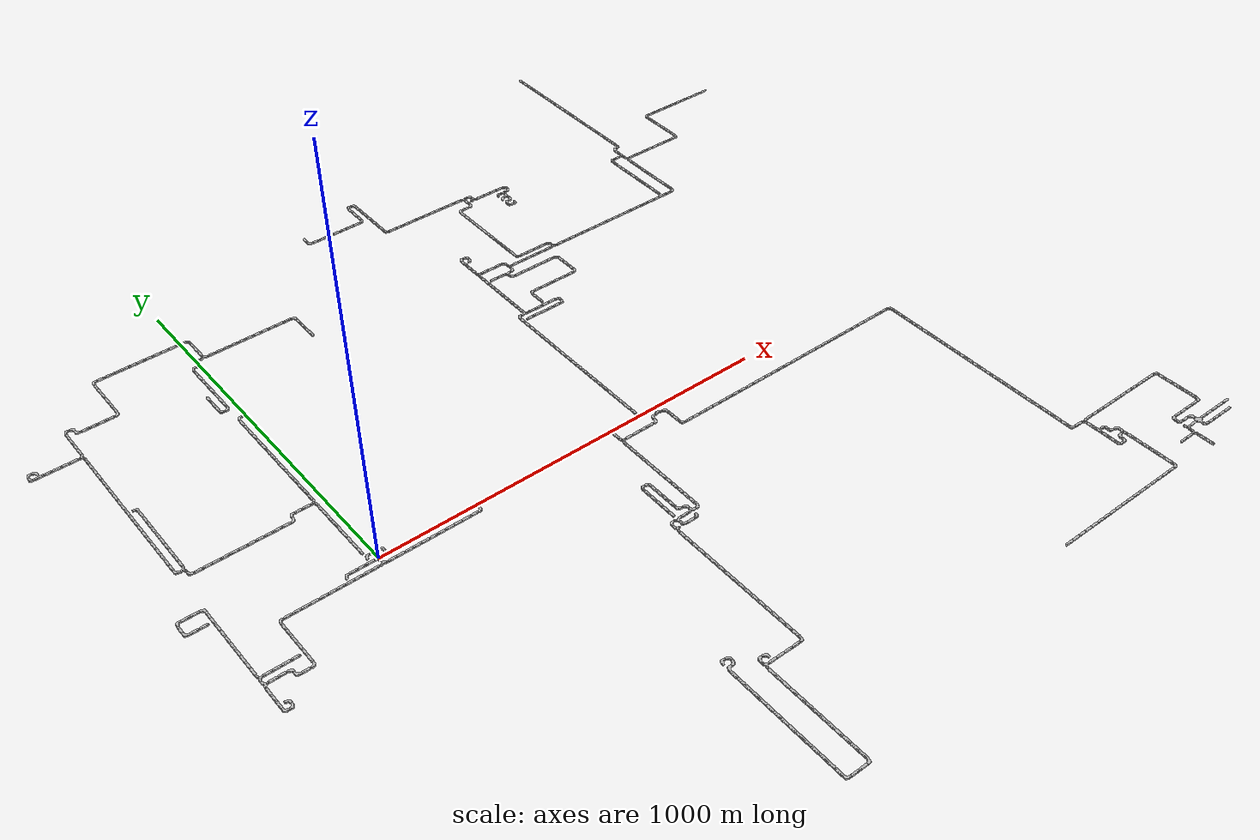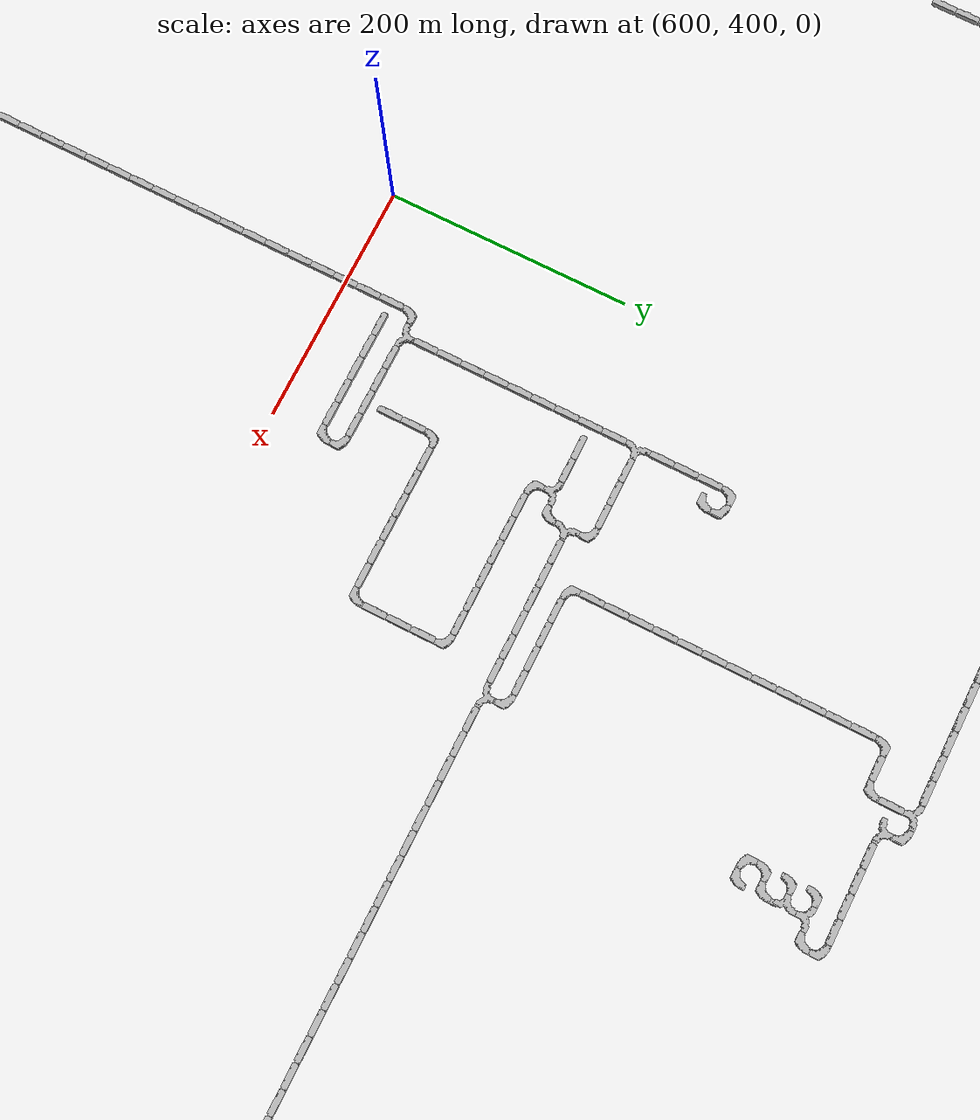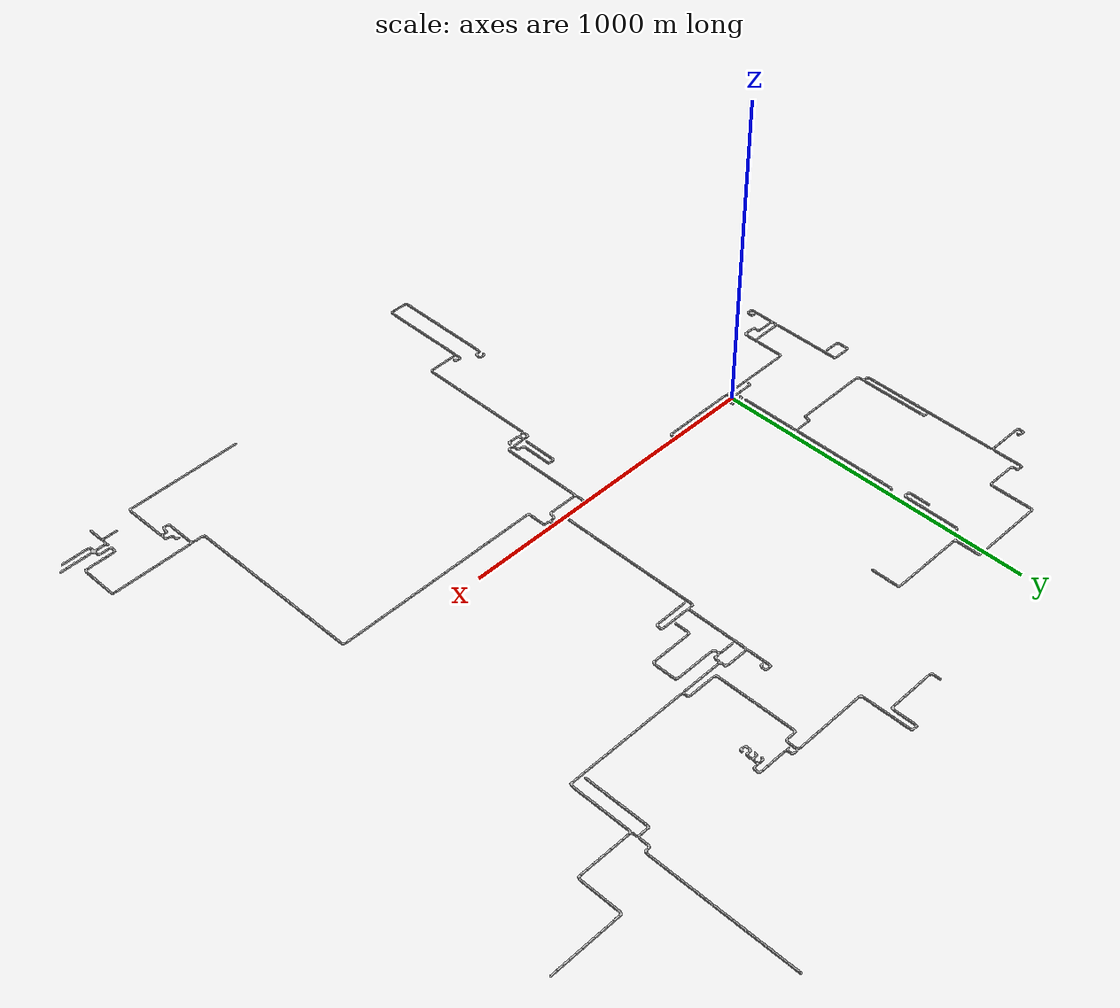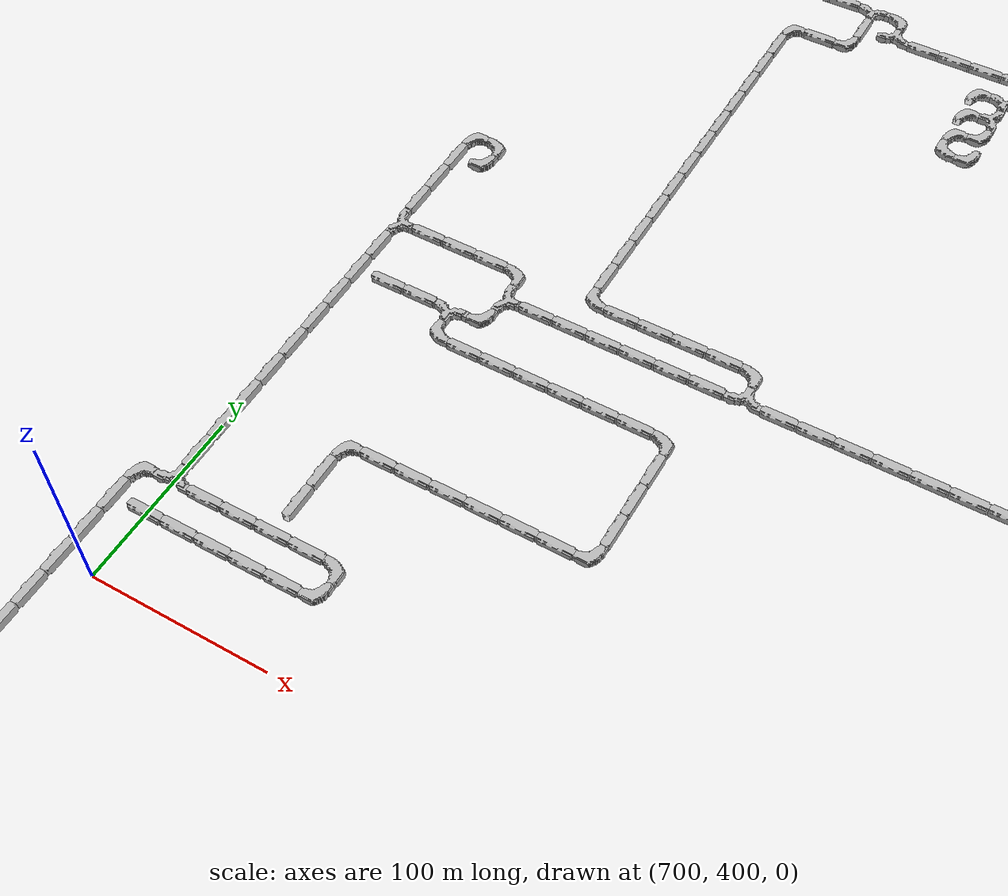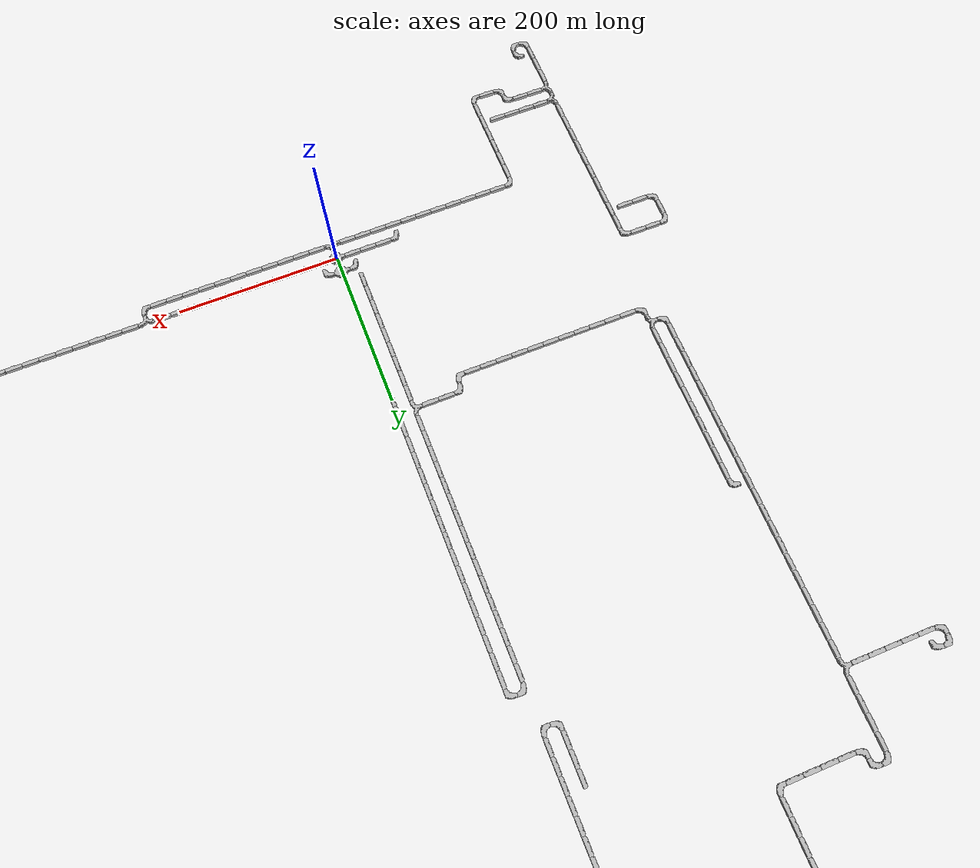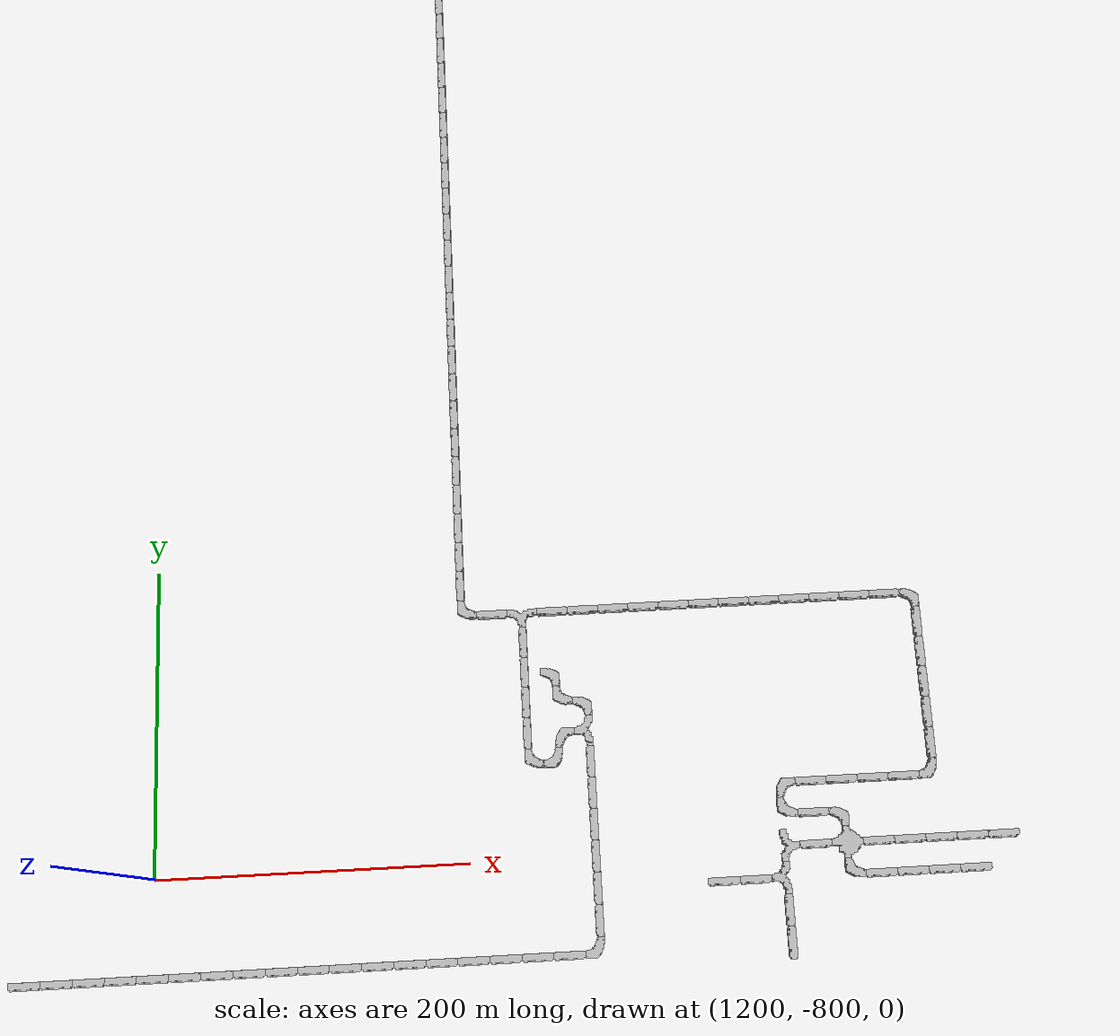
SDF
<sdf version="1.6">
 <world name="cave_16000_16">
  <include>
   <static>true</static>
   <name>cave_0_0</name>
   <pose>0 0 0 0 0 -1.5707963267948966</pose>
   <uri>model://cave_4way_20m</uri>
  </include>
  <include>
   <static>true</static>
   <name>cave_1_0</name>
   <pose>20 0 0 0 0 1.5707963267948966</pose>
   <uri>model://cave_straight_20m</uri>
  </include>
  <include>
   <static>true</static>
   <name>cave_2_0</name>
   <pose>40 0 0 0 0 1.5707963267948966</pose>
   <uri>model://cave_straight_20m</uri>
  </include>
  <include>
   <static>true</static>
   <name>cave_3_0</name>
   <pose>60 0 0 0 0 1.5707963267948966</pose>
   <uri>model://cave_straight_20m</uri>
  </include>
  <include>
   <static>true</static>
   <name>cave_4_0</name>
   <pose>80 0 0 0 0 1.5707963267948966</pose>
   <uri>model://cave_straight_20m</uri>
  </include>
  <include>
   <static>true</static>
   <name>cave_5_0</name>
   <pose>100 0 0 0 0 1.5707963267948966</pose>
   <uri>model://cave_straight_20m</uri>
  </include>
  <include>
   <static>true</static>
   <name>cave_6_0</name>
   <pose>120 0 0 0 0 1.5707963267948966</pose>
   <uri>model://cave_straight_20m</uri>
  </include>
  <include>
   <static>true</static>
   <name>cave_7_0</name>
   <pose>140 0 0 0 0 1.5707963267948966</pose>
   <uri>model://cave_straight_20m</uri>
  </include>
  <include>
   <static>true</static>
   <name>cave_8_0</name>
   <pose>160 0 0 0 0 1.5707963267948966</pose>
   <uri>model://cave_straight_20m</uri>
  </include>
  <include>
   <static>true</static>
   <name>cave_9_0</name>
   <pose>180 0 0 0 0 1.5707963267948966</pose>
   <uri>model://cave_straight_20m</uri>
  </include>
  <include>
   <static>true</static>
   <name>cave_10_0</name>
   <pose>200 0 0 0 0 1.5707963267948966</pose>
   <uri>model://cave_straight_20m</uri>
  </include>
  <include>
   <static>true</static>
   <name>cave_11_0</name>
   <pose>220 0 0 0 0 1.5707963267948966</pose>
   <uri>model://cave_straight_20m</uri>
  </include>
  <include>
   <static>true</static>
   <name>cave_12_0</name>
   <pose>240 0 0 0 0 3.141592653589793</pose>
   <uri>model://cave_3way_20m</uri>
  </include>
  <include>
   <static>true</static>
   <name>cave_13_0</name>
   <pose>260 0 0 0 0 1.5707963267948966</pose>
   <uri>model://cave_straight_20m</uri>
  </include>
  <include>
   <static>true</static>
   <name>cave_14_0</name>
   <pose>280 0 0 0 0 1.5707963267948966</pose>
   <uri>model://cave_straight_20m</uri>
  </include>
  <include>
   <static>true</static>
   <name>cave_15_0</name>
   <pose>300 0 0 0 0 1.5707963267948966</pose>
   <uri>model://cave_straight_20m</uri>
  </include>
  <include>
   <static>true</static>
   <name>cave_16_0</name>
   <pose>320 0 0 0 0 1.5707963267948966</pose>
   <uri>model://cave_straight_20m</uri>
  </include>
  <include>
   <static>true</static>
   <name>cave_17_0</name>
   <pose>340 0 0 0 0 1.5707963267948966</pose>
   <uri>model://cave_straight_20m</uri>
  </include>
  <include>
   <static>true</static>
   <name>cave_18_0</name>
   <pose>360 0 0 0 0 1.5707963267948966</pose>
   <uri>model://cave_straight_20m</uri>
  </include>
  <include>
   <static>true</static>
   <name>cave_19_0</name>
   <pose>380 0 0 0 0 1.5707963267948966</pose>
   <uri>model://cave_straight_20m</uri>
  </include>
  <include>
   <static>true</static>
   <name>cave_20_0</name>
   <pose>400 0 0 0 0 1.5707963267948966</pose>
   <uri>model://cave_straight_20m</uri>
  </include>
  <include>
   <static>true</static>
   <name>cave_21_0</name>
   <pose>420 0 0 0 0 1.5707963267948966</pose>
   <uri>model://cave_straight_20m</uri>
  </include>
  <include>
   <static>true</static>
   <name>cave_22_0</name>
   <pose>440 0 0 0 0 1.5707963267948966</pose>
   <uri>model://cave_straight_20m</uri>
  </include>
  <include>
   <static>true</static>
   <name>cave_23_0</name>
   <pose>460 0 0 0 0 1.5707963267948966</pose>
   <uri>model://cave_straight_20m</uri>
  </include>
  <include>
   <static>true</static>
   <name>cave_24_0</name>
   <pose>480 0 0 0 0 1.5707963267948966</pose>
   <uri>model://cave_straight_20m</uri>
  </include>
  <include>
   <static>true</static>
   <name>cave_25_0</name>
   <pose>500 0 0 0 0 1.5707963267948966</pose>
   <uri>model://cave_straight_20m</uri>
  </include>
  <include>
   <static>true</static>
   <name>cave_26_0</name>
   <pose>520 0 0 0 0 1.5707963267948966</pose>
   <uri>model://cave_straight_20m</uri>
  </include>
  <include>
   <static>true</static>
   <name>cave_27_0</name>
   <pose>540 0 0 0 0 1.5707963267948966</pose>
   <uri>model://cave_straight_20m</uri>
  </include>
  <include>
   <static>true</static>
   <name>cave_28_0</name>
   <pose>560 0 0 0 0 1.5707963267948966</pose>
   <uri>model://cave_straight_20m</uri>
  </include>
  <include>
   <static>true</static>
   <name>cave_29_0</name>
   <pose>580 0 0 0 0 1.5707963267948966</pose>
   <uri>model://cave_straight_20m</uri>
  </include>
  <include>
   <static>true</static>
   <name>cave_30_0</name>
   <pose>600 0 0 0 0 1.5707963267948966</pose>
   <uri>model://cave_straight_20m</uri>
  </include>
  <include>
   <static>true</static>
   <name>cave_31_0</name>
   <pose>620 0 0 0 0 1.5707963267948966</pose>
   <uri>model://cave_straight_20m</uri>
  </include>
  <include>
   <static>true</static>
   <name>cave_32_0</name>
   <pose>640 0 0 0 0 1.5707963267948966</pose>
   <uri>model://cave_straight_20m</uri>
  </include>
  <include>
   <static>true</static>
   <name>cave_33_0</name>
   <pose>660 0 0 0 0 1.5707963267948966</pose>
   <uri>model://cave_straight_20m</uri>
  </include>
  <include>
   <static>true</static>
   <name>cave_34_0</name>
   <pose>680 0 0 0 0 0.0</pose>
   <uri>model://cave_3way_20m</uri>
  </include>
  <include>
   <static>true</static>
   <name>cave_35_0</name>
   <pose>700 0 0 0 0 1.5707963267948966</pose>
   <uri>model://cave_straight_20m</uri>
  </include>
  <include>
   <static>true</static>
   <name>cave_36_0</name>
   <pose>720 0 0 0 0 3.141592653589793</pose>
   <uri>model://cave_L_20m</uri>
  </include>
  <include>
   <static>true</static>
   <name>cave_36_-1</name>
   <pose>720 -20 0 0 0 0.0</pose>
   <uri>model://cave_3way_20m</uri>
  </include>
  <include>
   <static>true</static>
   <name>cave_37_-1</name>
   <pose>740 -20 0 0 0 3.141592653589793</pose>
   <uri>model://cave_L_20m</uri>
  </include>
  <include>
   <static>true</static>
   <name>cave_37_-2</name>
   <pose>740 -40 0 0 0 0.0</pose>
   <uri>model://cave_straight_20m</uri>
  </include>
  <include>
   <static>true</static>
   <name>cave_37_-3</name>
   <pose>740 -60 0 0 0 0.0</pose>
   <uri>model://cave_straight_20m</uri>
  </include>
  <include>
   <static>true</static>
   <name>cave_37_-4</name>
   <pose>740 -80 0 0 0 0.0</pose>
   <uri>model://cave_L_20m</uri>
  </include>
  <include>
   <static>true</static>
   <name>cave_38_-4</name>
   <pose>760 -80 0 0 0 1.5707963267948966</pose>
   <uri>model://cave_straight_20m</uri>
  </include>
  <include>
   <static>true</static>
   <name>cave_39_-4</name>
   <pose>780 -80 0 0 0 1.5707963267948966</pose>
   <uri>model://cave_straight_20m</uri>
  </include>
  <include>
   <static>true</static>
   <name>cave_40_-4</name>
   <pose>800 -80 0 0 0 1.5707963267948966</pose>
   <uri>model://cave_straight_20m</uri>
  </include>
  <include>
   <static>true</static>
   <name>cave_41_-4</name>
   <pose>820 -80 0 0 0 1.5707963267948966</pose>
   <uri>model://cave_straight_20m</uri>
  </include>
  <include>
   <static>true</static>
   <name>cave_42_-4</name>
   <pose>840 -80 0 0 0 1.5707963267948966</pose>
   <uri>model://cave_straight_20m</uri>
  </include>
  <include>
   <static>true</static>
   <name>cave_43_-4</name>
   <pose>860 -80 0 0 0 1.5707963267948966</pose>
   <uri>model://cave_straight_20m</uri>
  </include>
  <include>
   <static>true</static>
   <name>cave_44_-4</name>
   <pose>880 -80 0 0 0 1.5707963267948966</pose>
   <uri>model://cave_straight_20m</uri>
  </include>
  <include>
   <static>true</static>
   <name>cave_45_-4</name>
   <pose>900 -80 0 0 0 1.5707963267948966</pose>
   <uri>model://cave_straight_20m</uri>
  </include>
  <include>
   <static>true</static>
   <name>cave_46_-4</name>
   <pose>920 -80 0 0 0 1.5707963267948966</pose>
   <uri>model://cave_straight_20m</uri>
  </include>
  <include>
   <static>true</static>
   <name>cave_47_-4</name>
   <pose>940 -80 0 0 0 1.5707963267948966</pose>
   <uri>model://cave_straight_20m</uri>
  </include>
  <include>
   <static>true</static>
   <name>cave_48_-4</name>
   <pose>960 -80 0 0 0 1.5707963267948966</pose>
   <uri>model://cave_straight_20m</uri>
  </include>
  <include>
   <static>true</static>
   <name>cave_49_-4</name>
   <pose>980 -80 0 0 0 1.5707963267948966</pose>
   <uri>model://cave_straight_20m</uri>
  </include>
  <include>
   <static>true</static>
   <name>cave_50_-4</name>
   <pose>1000 -80 0 0 0 1.5707963267948966</pose>
   <uri>model://cave_straight_20m</uri>
  </include>
  <include>
   <static>true</static>
   <name>cave_51_-4</name>
   <pose>1020 -80 0 0 0 1.5707963267948966</pose>
   <uri>model://cave_straight_20m</uri>
  </include>
  <include>
   <static>true</static>
   <name>cave_52_-4</name>
   <pose>1040 -80 0 0 0 1.5707963267948966</pose>
   <uri>model://cave_straight_20m</uri>
  </include>
  <include>
   <static>true</static>
   <name>cave_53_-4</name>
   <pose>1060 -80 0 0 0 1.5707963267948966</pose>
   <uri>model://cave_straight_20m</uri>
  </include>
  <include>
   <static>true</static>
   <name>cave_54_-4</name>
   <pose>1080 -80 0 0 0 1.5707963267948966</pose>
   <uri>model://cave_straight_20m</uri>
  </include>
  <include>
   <static>true</static>
   <name>cave_55_-4</name>
   <pose>1100 -80 0 0 0 1.5707963267948966</pose>
   <uri>model://cave_straight_20m</uri>
  </include>
  <include>
   <static>true</static>
   <name>cave_56_-4</name>
   <pose>1120 -80 0 0 0 1.5707963267948966</pose>
   <uri>model://cave_straight_20m</uri>
  </include>
  <include>
   <static>true</static>
   <name>cave_57_-4</name>
   <pose>1140 -80 0 0 0 1.5707963267948966</pose>
   <uri>model://cave_straight_20m</uri>
  </include>
  <include>
   <static>true</static>
   <name>cave_58_-4</name>
   <pose>1160 -80 0 0 0 1.5707963267948966</pose>
   <uri>model://cave_straight_20m</uri>
  </include>
  <include>
   <static>true</static>
   <name>cave_59_-4</name>
   <pose>1180 -80 0 0 0 1.5707963267948966</pose>
   <uri>model://cave_straight_20m</uri>
  </include>
  <include>
   <static>true</static>
   <name>cave_60_-4</name>
   <pose>1200 -80 0 0 0 1.5707963267948966</pose>
   <uri>model://cave_straight_20m</uri>
  </include>
  <include>
   <static>true</static>
   <name>cave_61_-4</name>
   <pose>1220 -80 0 0 0 1.5707963267948966</pose>
   <uri>model://cave_straight_20m</uri>
  </include>
  <include>
   <static>true</static>
   <name>cave_62_-4</name>
   <pose>1240 -80 0 0 0 1.5707963267948966</pose>
   <uri>model://cave_straight_20m</uri>
  </include>
  <include>
   <static>true</static>
   <name>cave_63_-4</name>
   <pose>1260 -80 0 0 0 1.5707963267948966</pose>
   <uri>model://cave_straight_20m</uri>
  </include>
  <include>
   <static>true</static>
   <name>cave_64_-4</name>
   <pose>1280 -80 0 0 0 1.5707963267948966</pose>
   <uri>model://cave_straight_20m</uri>
  </include>
  <include>
   <static>true</static>
   <name>cave_65_-4</name>
   <pose>1300 -80 0 0 0 1.5707963267948966</pose>
   <uri>model://cave_straight_20m</uri>
  </include>
  <include>
   <static>true</static>
   <name>cave_66_-4</name>
   <pose>1320 -80 0 0 0 1.5707963267948966</pose>
   <uri>model://cave_straight_20m</uri>
  </include>
  <include>
   <static>true</static>
   <name>cave_67_-4</name>
   <pose>1340 -80 0 0 0 1.5707963267948966</pose>
   <uri>model://cave_straight_20m</uri>
  </include>
  <include>
   <static>true</static>
   <name>cave_68_-4</name>
   <pose>1360 -80 0 0 0 1.5707963267948966</pose>
   <uri>model://cave_straight_20m</uri>
  </include>
  <include>
   <static>true</static>
   <name>cave_69_-4</name>
   <pose>1380 -80 0 0 0 1.5707963267948966</pose>
   <uri>model://cave_straight_20m</uri>
  </include>
  <include>
   <static>true</static>
   <name>cave_70_-4</name>
   <pose>1400 -80 0 0 0 3.141592653589793</pose>
   <uri>model://cave_L_20m</uri>
  </include>
  <include>
   <static>true</static>
   <name>cave_70_-5</name>
   <pose>1400 -100 0 0 0 0.0</pose>
   <uri>model://cave_straight_20m</uri>
  </include>
  <include>
   <static>true</static>
   <name>cave_70_-6</name>
   <pose>1400 -120 0 0 0 0.0</pose>
   <uri>model://cave_straight_20m</uri>
  </include>
  <include>
   <static>true</static>
   <name>cave_70_-7</name>
   <pose>1400 -140 0 0 0 0.0</pose>
   <uri>model://cave_straight_20m</uri>
  </include>
  <include>
   <static>true</static>
   <name>cave_70_-8</name>
   <pose>1400 -160 0 0 0 0.0</pose>
   <uri>model://cave_straight_20m</uri>
  </include>
  <include>
   <static>true</static>
   <name>cave_70_-9</name>
   <pose>1400 -180 0 0 0 0.0</pose>
   <uri>model://cave_straight_20m</uri>
  </include>
  <include>
   <static>true</static>
   <name>cave_70_-10</name>
   <pose>1400 -200 0 0 0 0.0</pose>
   <uri>model://cave_straight_20m</uri>
  </include>
  <include>
   <static>true</static>
   <name>cave_70_-11</name>
   <pose>1400 -220 0 0 0 0.0</pose>
   <uri>model://cave_straight_20m</uri>
  </include>
  <include>
   <static>true</static>
   <name>cave_70_-12</name>
   <pose>1400 -240 0 0 0 0.0</pose>
   <uri>model://cave_straight_20m</uri>
  </include>
  <include>
   <static>true</static>
   <name>cave_70_-13</name>
   <pose>1400 -260 0 0 0 0.0</pose>
   <uri>model://cave_straight_20m</uri>
  </include>
  <include>
   <static>true</static>
   <name>cave_70_-14</name>
   <pose>1400 -280 0 0 0 0.0</pose>
   <uri>model://cave_straight_20m</uri>
  </include>
  <include>
   <static>true</static>
   <name>cave_70_-15</name>
   <pose>1400 -300 0 0 0 0.0</pose>
   <uri>model://cave_straight_20m</uri>
  </include>
  <include>
   <static>true</static>
   <name>cave_70_-16</name>
   <pose>1400 -320 0 0 0 0.0</pose>
   <uri>model://cave_straight_20m</uri>
  </include>
  <include>
   <static>true</static>
   <name>cave_70_-17</name>
   <pose>1400 -340 0 0 0 0.0</pose>
   <uri>model://cave_straight_20m</uri>
  </include>
  <include>
   <static>true</static>
   <name>cave_70_-18</name>
   <pose>1400 -360 0 0 0 0.0</pose>
   <uri>model://cave_straight_20m</uri>
  </include>
  <include>
   <static>true</static>
   <name>cave_70_-19</name>
   <pose>1400 -380 0 0 0 0.0</pose>
   <uri>model://cave_straight_20m</uri>
  </include>
  <include>
   <static>true</static>
   <name>cave_70_-20</name>
   <pose>1400 -400 0 0 0 0.0</pose>
   <uri>model://cave_straight_20m</uri>
  </include>
  <include>
   <static>true</static>
   <name>cave_70_-21</name>
   <pose>1400 -420 0 0 0 0.0</pose>
   <uri>model://cave_straight_20m</uri>
  </include>
  <include>
   <static>true</static>
   <name>cave_70_-22</name>
   <pose>1400 -440 0 0 0 0.0</pose>
   <uri>model://cave_straight_20m</uri>
  </include>
  <include>
   <static>true</static>
   <name>cave_70_-23</name>
   <pose>1400 -460 0 0 0 0.0</pose>
   <uri>model://cave_straight_20m</uri>
  </include>
  <include>
   <static>true</static>
   <name>cave_70_-24</name>
   <pose>1400 -480 0 0 0 0.0</pose>
   <uri>model://cave_straight_20m</uri>
  </include>
  <include>
   <static>true</static>
   <name>cave_70_-25</name>
   <pose>1400 -500 0 0 0 0.0</pose>
   <uri>model://cave_straight_20m</uri>
  </include>
  <include>
   <static>true</static>
   <name>cave_70_-26</name>
   <pose>1400 -520 0 0 0 0.0</pose>
   <uri>model://cave_straight_20m</uri>
  </include>
  <include>
   <static>true</static>
   <name>cave_70_-27</name>
   <pose>1400 -540 0 0 0 0.0</pose>
   <uri>model://cave_straight_20m</uri>
  </include>
  <include>
   <static>true</static>
   <name>cave_70_-28</name>
   <pose>1400 -560 0 0 0 0.0</pose>
   <uri>model://cave_straight_20m</uri>
  </include>
  <include>
   <static>true</static>
   <name>cave_70_-29</name>
   <pose>1400 -580 0 0 0 0.0</pose>
   <uri>model://cave_straight_20m</uri>
  </include>
  <include>
   <static>true</static>
   <name>cave_70_-30</name>
   <pose>1400 -600 0 0 0 0.0</pose>
   <uri>model://cave_straight_20m</uri>
  </include>
  <include>
   <static>true</static>
   <name>cave_70_-31</name>
   <pose>1400 -620 0 0 0 0.0</pose>
   <uri>model://cave_straight_20m</uri>
  </include>
  <include>
   <static>true</static>
   <name>cave_70_-32</name>
   <pose>1400 -640 0 0 0 0.0</pose>
   <uri>model://cave_L_20m</uri>
  </include>
  <include>
   <static>true</static>
   <name>cave_71_-32</name>
   <pose>1420 -640 0 0 0 1.5707963267948966</pose>
   <uri>model://cave_straight_20m</uri>
  </include>
  <include>
   <static>true</static>
   <name>cave_72_-32</name>
   <pose>1440 -640 0 0 0 3.141592653589793</pose>
   <uri>model://cave_3way_20m</uri>
  </include>
  <include>
   <static>true</static>
   <name>cave_73_-32</name>
   <pose>1460 -640 0 0 0 1.5707963267948966</pose>
   <uri>model://cave_straight_20m</uri>
  </include>
  <include>
   <static>true</static>
   <name>cave_74_-32</name>
   <pose>1480 -640 0 0 0 1.5707963267948966</pose>
   <uri>model://cave_straight_20m</uri>
  </include>
  <include>
   <static>true</static>
   <name>cave_75_-32</name>
   <pose>1500 -640 0 0 0 1.5707963267948966</pose>
   <uri>model://cave_straight_20m</uri>
  </include>
  <include>
   <static>true</static>
   <name>cave_76_-32</name>
   <pose>1520 -640 0 0 0 1.5707963267948966</pose>
   <uri>model://cave_straight_20m</uri>
  </include>
  <include>
   <static>true</static>
   <name>cave_77_-32</name>
   <pose>1540 -640 0 0 0 1.5707963267948966</pose>
   <uri>model://cave_straight_20m</uri>
  </include>
  <include>
   <static>true</static>
   <name>cave_78_-32</name>
   <pose>1560 -640 0 0 0 1.5707963267948966</pose>
   <uri>model://cave_straight_20m</uri>
  </include>
  <include>
   <static>true</static>
   <name>cave_79_-32</name>
   <pose>1580 -640 0 0 0 1.5707963267948966</pose>
   <uri>model://cave_straight_20m</uri>
  </include>
  <include>
   <static>true</static>
   <name>cave_80_-32</name>
   <pose>1600 -640 0 0 0 1.5707963267948966</pose>
   <uri>model://cave_straight_20m</uri>
  </include>
  <include>
   <static>true</static>
   <name>cave_81_-32</name>
   <pose>1620 -640 0 0 0 1.5707963267948966</pose>
   <uri>model://cave_straight_20m</uri>
  </include>
  <include>
   <static>true</static>
   <name>cave_82_-32</name>
   <pose>1640 -640 0 0 0 1.5707963267948966</pose>
   <uri>model://cave_straight_20m</uri>
  </include>
  <include>
   <static>true</static>
   <name>cave_83_-32</name>
   <pose>1660 -640 0 0 0 1.5707963267948966</pose>
   <uri>model://cave_straight_20m</uri>
  </include>
  <include>
   <static>true</static>
   <name>cave_84_-32</name>
   <pose>1680 -640 0 0 0 1.5707963267948966</pose>
   <uri>model://cave_straight_20m</uri>
  </include>
  <include>
   <static>true</static>
   <name>cave_85_-32</name>
   <pose>1700 -640 0 0 0 3.141592653589793</pose>
   <uri>model://cave_L_20m</uri>
  </include>
  <include>
   <static>true</static>
   <name>cave_85_-33</name>
   <pose>1700 -660 0 0 0 0.0</pose>
   <uri>model://cave_straight_20m</uri>
  </include>
  <include>
   <static>true</static>
   <name>cave_85_-34</name>
   <pose>1700 -680 0 0 0 0.0</pose>
   <uri>model://cave_straight_20m</uri>
  </include>
  <include>
   <static>true</static>
   <name>cave_85_-35</name>
   <pose>1700 -700 0 0 0 0.0</pose>
   <uri>model://cave_straight_20m</uri>
  </include>
  <include>
   <static>true</static>
   <name>cave_85_-36</name>
   <pose>1700 -720 0 0 0 0.0</pose>
   <uri>model://cave_straight_20m</uri>
  </include>
  <include>
   <static>true</static>
   <name>cave_85_-37</name>
   <pose>1700 -740 0 0 0 0.0</pose>
   <uri>model://cave_straight_20m</uri>
  </include>
  <include>
   <static>true</static>
   <name>cave_85_-38</name>
   <pose>1700 -760 0 0 0 1.5707963267948966</pose>
   <uri>model://cave_L_20m</uri>
  </include>
  <include>
   <static>true</static>
   <name>cave_84_-38</name>
   <pose>1680 -760 0 0 0 1.5707963267948966</pose>
   <uri>model://cave_straight_20m</uri>
  </include>
  <include>
   <static>true</static>
   <name>cave_83_-38</name>
   <pose>1660 -760 0 0 0 1.5707963267948966</pose>
   <uri>model://cave_straight_20m</uri>
  </include>
  <include>
   <static>true</static>
   <name>cave_82_-38</name>
   <pose>1640 -760 0 0 0 1.5707963267948966</pose>
   <uri>model://cave_straight_20m</uri>
  </include>
  <include>
   <static>true</static>
   <name>cave_81_-38</name>
   <pose>1620 -760 0 0 0 1.5707963267948966</pose>
   <uri>model://cave_straight_20m</uri>
  </include>
  <include>
   <static>true</static>
   <name>cave_80_-38</name>
   <pose>1600 -760 0 0 0 -1.5707963267948966</pose>
   <uri>model://cave_L_20m</uri>
  </include>
  <include>
   <static>true</static>
   <name>cave_80_-39</name>
   <pose>1600 -780 0 0 0 0.0</pose>
   <uri>model://cave_L_20m</uri>
  </include>
  <include>
   <static>true</static>
   <name>cave_81_-39</name>
   <pose>1620 -780 0 0 0 1.5707963267948966</pose>
   <uri>model://cave_straight_20m</uri>
  </include>
  <include>
   <static>true</static>
   <name>cave_82_-39</name>
   <pose>1640 -780 0 0 0 3.141592653589793</pose>
   <uri>model://cave_L_20m</uri>
  </include>
  <include>
   <static>true</static>
   <name>cave_82_-40</name>
   <pose>1640 -800 0 0 0 -1.5707963267948966</pose>
   <uri>model://cave_4way_20m</uri>
  </include>
  <include>
   <static>true</static>
   <name>cave_83_-40</name>
   <pose>1660 -800 0 0 0 1.5707963267948966</pose>
   <uri>model://cave_straight_20m</uri>
  </include>
  <include>
   <static>true</static>
   <name>cave_84_-40</name>
   <pose>1680 -800 0 0 0 1.5707963267948966</pose>
   <uri>model://cave_straight_20m</uri>
  </include>
  <include>
   <static>true</static>
   <name>cave_85_-40</name>
   <pose>1700 -800 0 0 0 1.5707963267948966</pose>
   <uri>model://cave_straight_20m</uri>
  </include>
  <include>
   <static>true</static>
   <name>cave_86_-40</name>
   <pose>1720 -800 0 0 0 1.5707963267948966</pose>
   <uri>model://cave_straight_20m</uri>
  </include>
  <include>
   <static>true</static>
   <name>cave_87_-40</name>
   <pose>1740 -800 0 0 0 1.5707963267948966</pose>
   <uri>model://cave_straight_20m</uri>
  </include>
  <include>
   <static>true</static>
   <name>cave_82_-41</name>
   <pose>1640 -820 0 0 0 0.0</pose>
   <uri>model://cave_L_20m</uri>
  </include>
  <include>
   <static>true</static>
   <name>cave_83_-41</name>
   <pose>1660 -820 0 0 0 1.5707963267948966</pose>
   <uri>model://cave_straight_20m</uri>
  </include>
  <include>
   <static>true</static>
   <name>cave_84_-41</name>
   <pose>1680 -820 0 0 0 1.5707963267948966</pose>
   <uri>model://cave_straight_20m</uri>
  </include>
  <include>
   <static>true</static>
   <name>cave_85_-41</name>
   <pose>1700 -820 0 0 0 1.5707963267948966</pose>
   <uri>model://cave_straight_20m</uri>
  </include>
  <include>
   <static>true</static>
   <name>cave_86_-41</name>
   <pose>1720 -820 0 0 0 1.5707963267948966</pose>
   <uri>model://cave_straight_20m</uri>
  </include>
  <include>
   <static>true</static>
   <name>cave_81_-40</name>
   <pose>1620 -800 0 0 0 1.5707963267948966</pose>
   <uri>model://cave_straight_20m</uri>
  </include>
  <include>
   <static>true</static>
   <name>cave_80_-40</name>
   <pose>1600 -800 0 0 0 -1.5707963267948966</pose>
   <uri>model://cave_3way_20m</uri>
  </include>
  <include>
   <static>true</static>
   <name>cave_80_-41</name>
   <pose>1600 -820 0 0 0 1.5707963267948966</pose>
   <uri>model://cave_3way_20m</uri>
  </include>
  <include>
   <static>true</static>
   <name>cave_80_-42</name>
   <pose>1600 -840 0 0 0 0.0</pose>
   <uri>model://cave_straight_20m</uri>
  </include>
  <include>
   <static>true</static>
   <name>cave_80_-43</name>
   <pose>1600 -860 0 0 0 0.0</pose>
   <uri>model://cave_straight_20m</uri>
  </include>
  <include>
   <static>true</static>
   <name>cave_79_-41</name>
   <pose>1580 -820 0 0 0 1.5707963267948966</pose>
   <uri>model://cave_straight_20m</uri>
  </include>
  <include>
   <static>true</static>
   <name>cave_78_-41</name>
   <pose>1560 -820 0 0 0 1.5707963267948966</pose>
   <uri>model://cave_straight_20m</uri>
  </include>
  <include>
   <static>true</static>
   <name>cave_72_-33</name>
   <pose>1440 -660 0 0 0 0.0</pose>
   <uri>model://cave_straight_20m</uri>
  </include>
  <include>
   <static>true</static>
   <name>cave_72_-34</name>
   <pose>1440 -680 0 0 0 0.0</pose>
   <uri>model://cave_straight_20m</uri>
  </include>
  <include>
   <static>true</static>
   <name>cave_72_-35</name>
   <pose>1440 -700 0 0 0 0.0</pose>
   <uri>model://cave_straight_20m</uri>
  </include>
  <include>
   <static>true</static>
   <name>cave_72_-36</name>
   <pose>1440 -720 0 0 0 0.0</pose>
   <uri>model://cave_straight_20m</uri>
  </include>
  <include>
   <static>true</static>
   <name>cave_72_-37</name>
   <pose>1440 -740 0 0 0 0.0</pose>
   <uri>model://cave_L_20m</uri>
  </include>
  <include>
   <static>true</static>
   <name>cave_73_-37</name>
   <pose>1460 -740 0 0 0 1.5707963267948966</pose>
   <uri>model://cave_L_20m</uri>
  </include>
  <include>
   <static>true</static>
   <name>cave_73_-36</name>
   <pose>1460 -720 0 0 0 -1.5707963267948966</pose>
   <uri>model://cave_L_20m</uri>
  </include>
  <include>
   <static>true</static>
   <name>cave_74_-36</name>
   <pose>1480 -720 0 0 0 1.5707963267948966</pose>
   <uri>model://cave_3way_20m</uri>
  </include>
  <include>
   <static>true</static>
   <name>cave_74_-37</name>
   <pose>1480 -740 0 0 0 0.0</pose>
   <uri>model://cave_straight_20m</uri>
  </include>
  <include>
   <static>true</static>
   <name>cave_74_-38</name>
   <pose>1480 -760 0 0 0 0.0</pose>
   <uri>model://cave_straight_20m</uri>
  </include>
  <include>
   <static>true</static>
   <name>cave_74_-39</name>
   <pose>1480 -780 0 0 0 0.0</pose>
   <uri>model://cave_straight_20m</uri>
  </include>
  <include>
   <static>true</static>
   <name>cave_74_-40</name>
   <pose>1480 -800 0 0 0 0.0</pose>
   <uri>model://cave_straight_20m</uri>
  </include>
  <include>
   <static>true</static>
   <name>cave_74_-41</name>
   <pose>1480 -820 0 0 0 0.0</pose>
   <uri>model://cave_straight_20m</uri>
  </include>
  <include>
   <static>true</static>
   <name>cave_74_-42</name>
   <pose>1480 -840 0 0 0 0.0</pose>
   <uri>model://cave_straight_20m</uri>
  </include>
  <include>
   <static>true</static>
   <name>cave_74_-43</name>
   <pose>1480 -860 0 0 0 1.5707963267948966</pose>
   <uri>model://cave_L_20m</uri>
  </include>
  <include>
   <static>true</static>
   <name>cave_73_-43</name>
   <pose>1460 -860 0 0 0 1.5707963267948966</pose>
   <uri>model://cave_straight_20m</uri>
  </include>
  <include>
   <static>true</static>
   <name>cave_72_-43</name>
   <pose>1440 -860 0 0 0 1.5707963267948966</pose>
   <uri>model://cave_straight_20m</uri>
  </include>
  <include>
   <static>true</static>
   <name>cave_71_-43</name>
   <pose>1420 -860 0 0 0 1.5707963267948966</pose>
   <uri>model://cave_straight_20m</uri>
  </include>
  <include>
   <static>true</static>
   <name>cave_70_-43</name>
   <pose>1400 -860 0 0 0 1.5707963267948966</pose>
   <uri>model://cave_straight_20m</uri>
  </include>
  <include>
   <static>true</static>
   <name>cave_69_-43</name>
   <pose>1380 -860 0 0 0 1.5707963267948966</pose>
   <uri>model://cave_straight_20m</uri>
  </include>
  <include>
   <static>true</static>
   <name>cave_68_-43</name>
   <pose>1360 -860 0 0 0 1.5707963267948966</pose>
   <uri>model://cave_straight_20m</uri>
  </include>
  <include>
   <static>true</static>
   <name>cave_67_-43</name>
   <pose>1340 -860 0 0 0 1.5707963267948966</pose>
   <uri>model://cave_straight_20m</uri>
  </include>
  <include>
   <static>true</static>
   <name>cave_66_-43</name>
   <pose>1320 -860 0 0 0 1.5707963267948966</pose>
   <uri>model://cave_straight_20m</uri>
  </include>
  <include>
   <static>true</static>
   <name>cave_65_-43</name>
   <pose>1300 -860 0 0 0 1.5707963267948966</pose>
   <uri>model://cave_straight_20m</uri>
  </include>
  <include>
   <static>true</static>
   <name>cave_64_-43</name>
   <pose>1280 -860 0 0 0 1.5707963267948966</pose>
   <uri>model://cave_straight_20m</uri>
  </include>
  <include>
   <static>true</static>
   <name>cave_63_-43</name>
   <pose>1260 -860 0 0 0 1.5707963267948966</pose>
   <uri>model://cave_straight_20m</uri>
  </include>
  <include>
   <static>true</static>
   <name>cave_62_-43</name>
   <pose>1240 -860 0 0 0 1.5707963267948966</pose>
   <uri>model://cave_straight_20m</uri>
  </include>
  <include>
   <static>true</static>
   <name>cave_61_-43</name>
   <pose>1220 -860 0 0 0 1.5707963267948966</pose>
   <uri>model://cave_straight_20m</uri>
  </include>
  <include>
   <static>true</static>
   <name>cave_60_-43</name>
   <pose>1200 -860 0 0 0 1.5707963267948966</pose>
   <uri>model://cave_straight_20m</uri>
  </include>
  <include>
   <static>true</static>
   <name>cave_59_-43</name>
   <pose>1180 -860 0 0 0 1.5707963267948966</pose>
   <uri>model://cave_straight_20m</uri>
  </include>
  <include>
   <static>true</static>
   <name>cave_58_-43</name>
   <pose>1160 -860 0 0 0 1.5707963267948966</pose>
   <uri>model://cave_straight_20m</uri>
  </include>
  <include>
   <static>true</static>
   <name>cave_57_-43</name>
   <pose>1140 -860 0 0 0 1.5707963267948966</pose>
   <uri>model://cave_straight_20m</uri>
  </include>
  <include>
   <static>true</static>
   <name>cave_56_-43</name>
   <pose>1120 -860 0 0 0 1.5707963267948966</pose>
   <uri>model://cave_straight_20m</uri>
  </include>
  <include>
   <static>true</static>
   <name>cave_74_-35</name>
   <pose>1480 -700 0 0 0 3.141592653589793</pose>
   <uri>model://cave_L_20m</uri>
  </include>
  <include>
   <static>true</static>
   <name>cave_73_-35</name>
   <pose>1460 -700 0 0 0 0.0</pose>
   <uri>model://cave_L_20m</uri>
  </include>
  <include>
   <static>true</static>
   <name>cave_73_-34</name>
   <pose>1460 -680 0 0 0 3.141592653589793</pose>
   <uri>model://cave_L_20m</uri>
  </include>
  <include>
   <static>true</static>
   <name>cave_35_-1</name>
   <pose>700 -20 0 0 0 -1.5707963267948966</pose>
   <uri>model://cave_L_20m</uri>
  </include>
  <include>
   <static>true</static>
   <name>cave_35_-2</name>
   <pose>700 -40 0 0 0 1.5707963267948966</pose>
   <uri>model://cave_L_20m</uri>
  </include>
  <include>
   <static>true</static>
   <name>cave_34_-2</name>
   <pose>680 -40 0 0 0 1.5707963267948966</pose>
   <uri>model://cave_straight_20m</uri>
  </include>
  <include>
   <static>true</static>
   <name>cave_33_-2</name>
   <pose>660 -40 0 0 0 1.5707963267948966</pose>
   <uri>model://cave_straight_20m</uri>
  </include>
  <include>
   <static>true</static>
   <name>cave_32_-2</name>
   <pose>640 -40 0 0 0 1.5707963267948966</pose>
   <uri>model://cave_straight_20m</uri>
  </include>
  <include>
   <static>true</static>
   <name>cave_31_-2</name>
   <pose>620 -40 0 0 0 1.5707963267948966</pose>
   <uri>model://cave_straight_20m</uri>
  </include>
  <include>
   <static>true</static>
   <name>cave_30_-2</name>
   <pose>600 -40 0 0 0 -1.5707963267948966</pose>
   <uri>model://cave_3way_20m</uri>
  </include>
  <include>
   <static>true</static>
   <name>cave_30_-3</name>
   <pose>600 -60 0 0 0 0.0</pose>
   <uri>model://cave_straight_20m</uri>
  </include>
  <include>
   <static>true</static>
   <name>cave_30_-4</name>
   <pose>600 -80 0 0 0 0.0</pose>
   <uri>model://cave_straight_20m</uri>
  </include>
  <include>
   <static>true</static>
   <name>cave_30_-5</name>
   <pose>600 -100 0 0 0 0.0</pose>
   <uri>model://cave_straight_20m</uri>
  </include>
  <include>
   <static>true</static>
   <name>cave_30_-6</name>
   <pose>600 -120 0 0 0 0.0</pose>
   <uri>model://cave_straight_20m</uri>
  </include>
  <include>
   <static>true</static>
   <name>cave_30_-7</name>
   <pose>600 -140 0 0 0 0.0</pose>
   <uri>model://cave_straight_20m</uri>
  </include>
  <include>
   <static>true</static>
   <name>cave_30_-8</name>
   <pose>600 -160 0 0 0 0.0</pose>
   <uri>model://cave_straight_20m</uri>
  </include>
  <include>
   <static>true</static>
   <name>cave_30_-9</name>
   <pose>600 -180 0 0 0 0.0</pose>
   <uri>model://cave_straight_20m</uri>
  </include>
  <include>
   <static>true</static>
   <name>cave_30_-10</name>
   <pose>600 -200 0 0 0 0.0</pose>
   <uri>model://cave_straight_20m</uri>
  </include>
  <include>
   <static>true</static>
   <name>cave_30_-11</name>
   <pose>600 -220 0 0 0 0.0</pose>
   <uri>model://cave_straight_20m</uri>
  </include>
  <include>
   <static>true</static>
   <name>cave_30_-12</name>
   <pose>600 -240 0 0 0 0.0</pose>
   <uri>model://cave_straight_20m</uri>
  </include>
  <include>
   <static>true</static>
   <name>cave_30_-13</name>
   <pose>600 -260 0 0 0 0.0</pose>
   <uri>model://cave_straight_20m</uri>
  </include>
  <include>
   <static>true</static>
   <name>cave_30_-14</name>
   <pose>600 -280 0 0 0 0.0</pose>
   <uri>model://cave_straight_20m</uri>
  </include>
  <include>
   <static>true</static>
   <name>cave_30_-15</name>
   <pose>600 -300 0 0 0 1.5707963267948966</pose>
   <uri>model://cave_L_20m</uri>
  </include>
  <include>
   <static>true</static>
   <name>cave_29_-15</name>
   <pose>580 -300 0 0 0 0.0</pose>
   <uri>model://cave_3way_20m</uri>
  </include>
  <include>
   <static>true</static>
   <name>cave_28_-15</name>
   <pose>560 -300 0 0 0 1.5707963267948966</pose>
   <uri>model://cave_straight_20m</uri>
  </include>
  <include>
   <static>true</static>
   <name>cave_27_-15</name>
   <pose>540 -300 0 0 0 3.141592653589793</pose>
   <uri>model://cave_3way_20m</uri>
  </include>
  <include>
   <static>true</static>
   <name>cave_27_-16</name>
   <pose>540 -320 0 0 0 0.0</pose>
   <uri>model://cave_L_20m</uri>
  </include>
  <include>
   <static>true</static>
   <name>cave_28_-16</name>
   <pose>560 -320 0 0 0 1.5707963267948966</pose>
   <uri>model://cave_straight_20m</uri>
  </include>
  <include>
   <static>true</static>
   <name>cave_29_-16</name>
   <pose>580 -320 0 0 0 1.5707963267948966</pose>
   <uri>model://cave_L_20m</uri>
  </include>
  <include>
   <static>true</static>
   <name>cave_26_-15</name>
   <pose>520 -300 0 0 0 -1.5707963267948966</pose>
   <uri>model://cave_L_20m</uri>
  </include>
  <include>
   <static>true</static>
   <name>cave_26_-16</name>
   <pose>520 -320 0 0 0 -1.5707963267948966</pose>
   <uri>model://cave_3way_20m</uri>
  </include>
  <include>
   <static>true</static>
   <name>cave_26_-17</name>
   <pose>520 -340 0 0 0 0.0</pose>
   <uri>model://cave_straight_20m</uri>
  </include>
  <include>
   <static>true</static>
   <name>cave_26_-18</name>
   <pose>520 -360 0 0 0 0.0</pose>
   <uri>model://cave_straight_20m</uri>
  </include>
  <include>
   <static>true</static>
   <name>cave_26_-19</name>
   <pose>520 -380 0 0 0 0.0</pose>
   <uri>model://cave_straight_20m</uri>
  </include>
  <include>
   <static>true</static>
   <name>cave_26_-20</name>
   <pose>520 -400 0 0 0 0.0</pose>
   <uri>model://cave_straight_20m</uri>
  </include>
  <include>
   <static>true</static>
   <name>cave_26_-21</name>
   <pose>520 -420 0 0 0 0.0</pose>
   <uri>model://cave_straight_20m</uri>
  </include>
  <include>
   <static>true</static>
   <name>cave_26_-22</name>
   <pose>520 -440 0 0 0 0.0</pose>
   <uri>model://cave_straight_20m</uri>
  </include>
  <include>
   <static>true</static>
   <name>cave_26_-23</name>
   <pose>520 -460 0 0 0 0.0</pose>
   <uri>model://cave_straight_20m</uri>
  </include>
  <include>
   <static>true</static>
   <name>cave_26_-24</name>
   <pose>520 -480 0 0 0 0.0</pose>
   <uri>model://cave_straight_20m</uri>
  </include>
  <include>
   <static>true</static>
   <name>cave_26_-25</name>
   <pose>520 -500 0 0 0 0.0</pose>
   <uri>model://cave_straight_20m</uri>
  </include>
  <include>
   <static>true</static>
   <name>cave_26_-26</name>
   <pose>520 -520 0 0 0 0.0</pose>
   <uri>model://cave_straight_20m</uri>
  </include>
  <include>
   <static>true</static>
   <name>cave_26_-27</name>
   <pose>520 -540 0 0 0 0.0</pose>
   <uri>model://cave_straight_20m</uri>
  </include>
  <include>
   <static>true</static>
   <name>cave_26_-28</name>
   <pose>520 -560 0 0 0 0.0</pose>
   <uri>model://cave_straight_20m</uri>
  </include>
  <include>
   <static>true</static>
   <name>cave_26_-29</name>
   <pose>520 -580 0 0 0 0.0</pose>
   <uri>model://cave_straight_20m</uri>
  </include>
  <include>
   <static>true</static>
   <name>cave_26_-30</name>
   <pose>520 -600 0 0 0 0.0</pose>
   <uri>model://cave_straight_20m</uri>
  </include>
  <include>
   <static>true</static>
   <name>cave_26_-31</name>
   <pose>520 -620 0 0 0 0.0</pose>
   <uri>model://cave_straight_20m</uri>
  </include>
  <include>
   <static>true</static>
   <name>cave_26_-32</name>
   <pose>520 -640 0 0 0 0.0</pose>
   <uri>model://cave_straight_20m</uri>
  </include>
  <include>
   <static>true</static>
   <name>cave_26_-33</name>
   <pose>520 -660 0 0 0 0.0</pose>
   <uri>model://cave_straight_20m</uri>
  </include>
  <include>
   <static>true</static>
   <name>cave_26_-34</name>
   <pose>520 -680 0 0 0 0.0</pose>
   <uri>model://cave_straight_20m</uri>
  </include>
  <include>
   <static>true</static>
   <name>cave_26_-35</name>
   <pose>520 -700 0 0 0 1.5707963267948966</pose>
   <uri>model://cave_L_20m</uri>
  </include>
  <include>
   <static>true</static>
   <name>cave_25_-35</name>
   <pose>500 -700 0 0 0 1.5707963267948966</pose>
   <uri>model://cave_straight_20m</uri>
  </include>
  <include>
   <static>true</static>
   <name>cave_24_-35</name>
   <pose>480 -700 0 0 0 1.5707963267948966</pose>
   <uri>model://cave_straight_20m</uri>
  </include>
  <include>
   <static>true</static>
   <name>cave_23_-35</name>
   <pose>460 -700 0 0 0 1.5707963267948966</pose>
   <uri>model://cave_straight_20m</uri>
  </include>
  <include>
   <static>true</static>
   <name>cave_22_-35</name>
   <pose>440 -700 0 0 0 1.5707963267948966</pose>
   <uri>model://cave_straight_20m</uri>
  </include>
  <include>
   <static>true</static>
   <name>cave_21_-35</name>
   <pose>420 -700 0 0 0 -1.5707963267948966</pose>
   <uri>model://cave_3way_20m</uri>
  </include>
  <include>
   <static>true</static>
   <name>cave_21_-36</name>
   <pose>420 -720 0 0 0 0.0</pose>
   <uri>model://cave_straight_20m</uri>
  </include>
  <include>
   <static>true</static>
   <name>cave_21_-37</name>
   <pose>420 -740 0 0 0 0.0</pose>
   <uri>model://cave_straight_20m</uri>
  </include>
  <include>
   <static>true</static>
   <name>cave_21_-38</name>
   <pose>420 -760 0 0 0 0.0</pose>
   <uri>model://cave_straight_20m</uri>
  </include>
  <include>
   <static>true</static>
   <name>cave_21_-39</name>
   <pose>420 -780 0 0 0 0.0</pose>
   <uri>model://cave_straight_20m</uri>
  </include>
  <include>
   <static>true</static>
   <name>cave_21_-40</name>
   <pose>420 -800 0 0 0 0.0</pose>
   <uri>model://cave_straight_20m</uri>
  </include>
  <include>
   <static>true</static>
   <name>cave_21_-41</name>
   <pose>420 -820 0 0 0 0.0</pose>
   <uri>model://cave_straight_20m</uri>
  </include>
  <include>
   <static>true</static>
   <name>cave_21_-42</name>
   <pose>420 -840 0 0 0 0.0</pose>
   <uri>model://cave_straight_20m</uri>
  </include>
  <include>
   <static>true</static>
   <name>cave_21_-43</name>
   <pose>420 -860 0 0 0 0.0</pose>
   <uri>model://cave_straight_20m</uri>
  </include>
  <include>
   <static>true</static>
   <name>cave_21_-44</name>
   <pose>420 -880 0 0 0 0.0</pose>
   <uri>model://cave_straight_20m</uri>
  </include>
  <include>
   <static>true</static>
   <name>cave_21_-45</name>
   <pose>420 -900 0 0 0 0.0</pose>
   <uri>model://cave_straight_20m</uri>
  </include>
  <include>
   <static>true</static>
   <name>cave_21_-46</name>
   <pose>420 -920 0 0 0 0.0</pose>
   <uri>model://cave_straight_20m</uri>
  </include>
  <include>
   <static>true</static>
   <name>cave_21_-47</name>
   <pose>420 -940 0 0 0 0.0</pose>
   <uri>model://cave_straight_20m</uri>
  </include>
  <include>
   <static>true</static>
   <name>cave_21_-48</name>
   <pose>420 -960 0 0 0 0.0</pose>
   <uri>model://cave_straight_20m</uri>
  </include>
  <include>
   <static>true</static>
   <name>cave_21_-49</name>
   <pose>420 -980 0 0 0 1.5707963267948966</pose>
   <uri>model://cave_L_20m</uri>
  </include>
  <include>
   <static>true</static>
   <name>cave_20_-49</name>
   <pose>400 -980 0 0 0 1.5707963267948966</pose>
   <uri>model://cave_straight_20m</uri>
  </include>
  <include>
   <static>true</static>
   <name>cave_19_-49</name>
   <pose>380 -980 0 0 0 1.5707963267948966</pose>
   <uri>model://cave_straight_20m</uri>
  </include>
  <include>
   <static>true</static>
   <name>cave_18_-49</name>
   <pose>360 -980 0 0 0 0.0</pose>
   <uri>model://cave_L_20m</uri>
  </include>
  <include>
   <static>true</static>
   <name>cave_18_-48</name>
   <pose>360 -960 0 0 0 0.0</pose>
   <uri>model://cave_straight_20m</uri>
  </include>
  <include>
   <static>true</static>
   <name>cave_18_-47</name>
   <pose>360 -940 0 0 0 0.0</pose>
   <uri>model://cave_straight_20m</uri>
  </include>
  <include>
   <static>true</static>
   <name>cave_18_-46</name>
   <pose>360 -920 0 0 0 0.0</pose>
   <uri>model://cave_straight_20m</uri>
  </include>
  <include>
   <static>true</static>
   <name>cave_18_-45</name>
   <pose>360 -900 0 0 0 0.0</pose>
   <uri>model://cave_straight_20m</uri>
  </include>
  <include>
   <static>true</static>
   <name>cave_18_-44</name>
   <pose>360 -880 0 0 0 0.0</pose>
   <uri>model://cave_straight_20m</uri>
  </include>
  <include>
   <static>true</static>
   <name>cave_18_-43</name>
   <pose>360 -860 0 0 0 0.0</pose>
   <uri>model://cave_straight_20m</uri>
  </include>
  <include>
   <static>true</static>
   <name>cave_18_-42</name>
   <pose>360 -840 0 0 0 0.0</pose>
   <uri>model://cave_straight_20m</uri>
  </include>
  <include>
   <static>true</static>
   <name>cave_18_-41</name>
   <pose>360 -820 0 0 0 0.0</pose>
   <uri>model://cave_straight_20m</uri>
  </include>
  <include>
   <static>true</static>
   <name>cave_18_-40</name>
   <pose>360 -800 0 0 0 0.0</pose>
   <uri>model://cave_straight_20m</uri>
  </include>
  <include>
   <static>true</static>
   <name>cave_18_-39</name>
   <pose>360 -780 0 0 0 0.0</pose>
   <uri>model://cave_straight_20m</uri>
  </include>
  <include>
   <static>true</static>
   <name>cave_18_-38</name>
   <pose>360 -760 0 0 0 0.0</pose>
   <uri>model://cave_straight_20m</uri>
  </include>
  <include>
   <static>true</static>
   <name>cave_18_-37</name>
   <pose>360 -740 0 0 0 0.0</pose>
   <uri>model://cave_straight_20m</uri>
  </include>
  <include>
   <static>true</static>
   <name>cave_18_-36</name>
   <pose>360 -720 0 0 0 0.0</pose>
   <uri>model://cave_straight_20m</uri>
  </include>
  <include>
   <static>true</static>
   <name>cave_18_-35</name>
   <pose>360 -700 0 0 0 0.0</pose>
   <uri>model://cave_straight_20m</uri>
  </include>
  <include>
   <static>true</static>
   <name>cave_18_-34</name>
   <pose>360 -680 0 0 0 0.0</pose>
   <uri>model://cave_straight_20m</uri>
  </include>
  <include>
   <static>true</static>
   <name>cave_18_-33</name>
   <pose>360 -660 0 0 0 -1.5707963267948966</pose>
   <uri>model://cave_L_20m</uri>
  </include>
  <include>
   <static>true</static>
   <name>cave_19_-33</name>
   <pose>380 -660 0 0 0 1.5707963267948966</pose>
   <uri>model://cave_L_20m</uri>
  </include>
  <include>
   <static>true</static>
   <name>cave_19_-32</name>
   <pose>380 -640 0 0 0 3.141592653589793</pose>
   <uri>model://cave_L_20m</uri>
  </include>
  <include>
   <static>true</static>
   <name>cave_18_-32</name>
   <pose>360 -640 0 0 0 -1.5707963267948966</pose>
   <uri>model://cave_L_20m</uri>
  </include>
  <include>
   <static>true</static>
   <name>cave_21_-34</name>
   <pose>420 -680 0 0 0 -1.5707963267948966</pose>
   <uri>model://cave_L_20m</uri>
  </include>
  <include>
   <static>true</static>
   <name>cave_22_-34</name>
   <pose>440 -680 0 0 0 3.141592653589793</pose>
   <uri>model://cave_L_20m</uri>
  </include>
  <include>
   <static>true</static>
   <name>cave_29_-14</name>
   <pose>580 -280 0 0 0 3.141592653589793</pose>
   <uri>model://cave_L_20m</uri>
  </include>
  <include>
   <static>true</static>
   <name>cave_28_-14</name>
   <pose>560 -280 0 0 0 0.0</pose>
   <uri>model://cave_L_20m</uri>
  </include>
  <include>
   <static>true</static>
   <name>cave_28_-13</name>
   <pose>560 -260 0 0 0 0.0</pose>
   <uri>model://cave_straight_20m</uri>
  </include>
  <include>
   <static>true</static>
   <name>cave_28_-12</name>
   <pose>560 -240 0 0 0 0.0</pose>
   <uri>model://cave_straight_20m</uri>
  </include>
  <include>
   <static>true</static>
   <name>cave_28_-11</name>
   <pose>560 -220 0 0 0 0.0</pose>
   <uri>model://cave_straight_20m</uri>
  </include>
  <include>
   <static>true</static>
   <name>cave_28_-10</name>
   <pose>560 -200 0 0 0 0.0</pose>
   <uri>model://cave_straight_20m</uri>
  </include>
  <include>
   <static>true</static>
   <name>cave_28_-9</name>
   <pose>560 -180 0 0 0 3.141592653589793</pose>
   <uri>model://cave_L_20m</uri>
  </include>
  <include>
   <static>true</static>
   <name>cave_27_-9</name>
   <pose>540 -180 0 0 0 -1.5707963267948966</pose>
   <uri>model://cave_L_20m</uri>
  </include>
  <include>
   <static>true</static>
   <name>cave_27_-10</name>
   <pose>540 -200 0 0 0 0.0</pose>
   <uri>model://cave_straight_20m</uri>
  </include>
  <include>
   <static>true</static>
   <name>cave_27_-11</name>
   <pose>540 -220 0 0 0 0.0</pose>
   <uri>model://cave_straight_20m</uri>
  </include>
  <include>
   <static>true</static>
   <name>cave_27_-12</name>
   <pose>540 -240 0 0 0 0.0</pose>
   <uri>model://cave_straight_20m</uri>
  </include>
  <include>
   <static>true</static>
   <name>cave_27_-13</name>
   <pose>540 -260 0 0 0 0.0</pose>
   <uri>model://cave_straight_20m</uri>
  </include>
  <include>
   <static>true</static>
   <name>cave_27_-14</name>
   <pose>540 -280 0 0 0 0.0</pose>
   <uri>model://cave_straight_20m</uri>
  </include>
  <include>
   <static>true</static>
   <name>cave_30_-1</name>
   <pose>600 -20 0 0 0 0.0</pose>
   <uri>model://cave_straight_20m</uri>
  </include>
  <include>
   <static>true</static>
   <name>cave_34_1</name>
   <pose>680 20 0 0 0 0.0</pose>
   <uri>model://cave_straight_20m</uri>
  </include>
  <include>
   <static>true</static>
   <name>cave_34_2</name>
   <pose>680 40 0 0 0 0.0</pose>
   <uri>model://cave_straight_20m</uri>
  </include>
  <include>
   <static>true</static>
   <name>cave_34_3</name>
   <pose>680 60 0 0 0 0.0</pose>
   <uri>model://cave_straight_20m</uri>
  </include>
  <include>
   <static>true</static>
   <name>cave_34_4</name>
   <pose>680 80 0 0 0 0.0</pose>
   <uri>model://cave_straight_20m</uri>
  </include>
  <include>
   <static>true</static>
   <name>cave_34_5</name>
   <pose>680 100 0 0 0 0.0</pose>
   <uri>model://cave_straight_20m</uri>
  </include>
  <include>
   <static>true</static>
   <name>cave_34_6</name>
   <pose>680 120 0 0 0 0.0</pose>
   <uri>model://cave_straight_20m</uri>
  </include>
  <include>
   <static>true</static>
   <name>cave_34_7</name>
   <pose>680 140 0 0 0 0.0</pose>
   <uri>model://cave_straight_20m</uri>
  </include>
  <include>
   <static>true</static>
   <name>cave_34_8</name>
   <pose>680 160 0 0 0 0.0</pose>
   <uri>model://cave_straight_20m</uri>
  </include>
  <include>
   <static>true</static>
   <name>cave_34_9</name>
   <pose>680 180 0 0 0 0.0</pose>
   <uri>model://cave_straight_20m</uri>
  </include>
  <include>
   <static>true</static>
   <name>cave_34_10</name>
   <pose>680 200 0 0 0 0.0</pose>
   <uri>model://cave_straight_20m</uri>
  </include>
  <include>
   <static>true</static>
   <name>cave_34_11</name>
   <pose>680 220 0 0 0 0.0</pose>
   <uri>model://cave_straight_20m</uri>
  </include>
  <include>
   <static>true</static>
   <name>cave_34_12</name>
   <pose>680 240 0 0 0 0.0</pose>
   <uri>model://cave_straight_20m</uri>
  </include>
  <include>
   <static>true</static>
   <name>cave_34_13</name>
   <pose>680 260 0 0 0 0.0</pose>
   <uri>model://cave_straight_20m</uri>
  </include>
  <include>
   <static>true</static>
   <name>cave_34_14</name>
   <pose>680 280 0 0 0 0.0</pose>
   <uri>model://cave_straight_20m</uri>
  </include>
  <include>
   <static>true</static>
   <name>cave_34_15</name>
   <pose>680 300 0 0 0 0.0</pose>
   <uri>model://cave_straight_20m</uri>
  </include>
  <include>
   <static>true</static>
   <name>cave_34_16</name>
   <pose>680 320 0 0 0 0.0</pose>
   <uri>model://cave_straight_20m</uri>
  </include>
  <include>
   <static>true</static>
   <name>cave_34_17</name>
   <pose>680 340 0 0 0 0.0</pose>
   <uri>model://cave_straight_20m</uri>
  </include>
  <include>
   <static>true</static>
   <name>cave_34_18</name>
   <pose>680 360 0 0 0 0.0</pose>
   <uri>model://cave_straight_20m</uri>
  </include>
  <include>
   <static>true</static>
   <name>cave_34_19</name>
   <pose>680 380 0 0 0 0.0</pose>
   <uri>model://cave_straight_20m</uri>
  </include>
  <include>
   <static>true</static>
   <name>cave_34_20</name>
   <pose>680 400 0 0 0 0.0</pose>
   <uri>model://cave_straight_20m</uri>
  </include>
  <include>
   <static>true</static>
   <name>cave_34_21</name>
   <pose>680 420 0 0 0 0.0</pose>
   <uri>model://cave_straight_20m</uri>
  </include>
  <include>
   <static>true</static>
   <name>cave_34_22</name>
   <pose>680 440 0 0 0 0.0</pose>
   <uri>model://cave_straight_20m</uri>
  </include>
  <include>
   <static>true</static>
   <name>cave_34_23</name>
   <pose>680 460 0 0 0 -1.5707963267948966</pose>
   <uri>model://cave_L_20m</uri>
  </include>
  <include>
   <static>true</static>
   <name>cave_35_23</name>
   <pose>700 460 0 0 0 0.0</pose>
   <uri>model://cave_3way_20m</uri>
  </include>
  <include>
   <static>true</static>
   <name>cave_36_23</name>
   <pose>720 460 0 0 0 1.5707963267948966</pose>
   <uri>model://cave_straight_20m</uri>
  </include>
  <include>
   <static>true</static>
   <name>cave_37_23</name>
   <pose>740 460 0 0 0 1.5707963267948966</pose>
   <uri>model://cave_straight_20m</uri>
  </include>
  <include>
   <static>true</static>
   <name>cave_38_23</name>
   <pose>760 460 0 0 0 1.5707963267948966</pose>
   <uri>model://cave_straight_20m</uri>
  </include>
  <include>
   <static>true</static>
   <name>cave_39_23</name>
   <pose>780 460 0 0 0 1.5707963267948966</pose>
   <uri>model://cave_straight_20m</uri>
  </include>
  <include>
   <static>true</static>
   <name>cave_40_23</name>
   <pose>800 460 0 0 0 3.141592653589793</pose>
   <uri>model://cave_L_20m</uri>
  </include>
  <include>
   <static>true</static>
   <name>cave_40_22</name>
   <pose>800 440 0 0 0 1.5707963267948966</pose>
   <uri>model://cave_L_20m</uri>
  </include>
  <include>
   <static>true</static>
   <name>cave_39_22</name>
   <pose>780 440 0 0 0 1.5707963267948966</pose>
   <uri>model://cave_straight_20m</uri>
  </include>
  <include>
   <static>true</static>
   <name>cave_38_22</name>
   <pose>760 440 0 0 0 1.5707963267948966</pose>
   <uri>model://cave_straight_20m</uri>
  </include>
  <include>
   <static>true</static>
   <name>cave_37_22</name>
   <pose>740 440 0 0 0 1.5707963267948966</pose>
   <uri>model://cave_straight_20m</uri>
  </include>
  <include>
   <static>true</static>
   <name>cave_36_22</name>
   <pose>720 440 0 0 0 1.5707963267948966</pose>
   <uri>model://cave_straight_20m</uri>
  </include>
  <include>
   <static>true</static>
   <name>cave_35_22</name>
   <pose>700 440 0 0 0 1.5707963267948966</pose>
   <uri>model://cave_straight_20m</uri>
  </include>
  <include>
   <static>true</static>
   <name>cave_35_24</name>
   <pose>700 480 0 0 0 0.0</pose>
   <uri>model://cave_straight_20m</uri>
  </include>
  <include>
   <static>true</static>
   <name>cave_35_25</name>
   <pose>700 500 0 0 0 0.0</pose>
   <uri>model://cave_straight_20m</uri>
  </include>
  <include>
   <static>true</static>
   <name>cave_35_26</name>
   <pose>700 520 0 0 0 0.0</pose>
   <uri>model://cave_straight_20m</uri>
  </include>
  <include>
   <static>true</static>
   <name>cave_35_27</name>
   <pose>700 540 0 0 0 0.0</pose>
   <uri>model://cave_straight_20m</uri>
  </include>
  <include>
   <static>true</static>
   <name>cave_35_28</name>
   <pose>700 560 0 0 0 0.0</pose>
   <uri>model://cave_straight_20m</uri>
  </include>
  <include>
   <static>true</static>
   <name>cave_35_29</name>
   <pose>700 580 0 0 0 0.0</pose>
   <uri>model://cave_straight_20m</uri>
  </include>
  <include>
   <static>true</static>
   <name>cave_35_30</name>
   <pose>700 600 0 0 0 0.0</pose>
   <uri>model://cave_straight_20m</uri>
  </include>
  <include>
   <static>true</static>
   <name>cave_35_31</name>
   <pose>700 620 0 0 0 0.0</pose>
   <uri>model://cave_straight_20m</uri>
  </include>
  <include>
   <static>true</static>
   <name>cave_35_32</name>
   <pose>700 640 0 0 0 0.0</pose>
   <uri>model://cave_straight_20m</uri>
  </include>
  <include>
   <static>true</static>
   <name>cave_35_33</name>
   <pose>700 660 0 0 0 -1.5707963267948966</pose>
   <uri>model://cave_3way_20m</uri>
  </include>
  <include>
   <static>true</static>
   <name>cave_36_33</name>
   <pose>720 660 0 0 0 1.5707963267948966</pose>
   <uri>model://cave_straight_20m</uri>
  </include>
  <include>
   <static>true</static>
   <name>cave_37_33</name>
   <pose>740 660 0 0 0 1.5707963267948966</pose>
   <uri>model://cave_straight_20m</uri>
  </include>
  <include>
   <static>true</static>
   <name>cave_38_33</name>
   <pose>760 660 0 0 0 1.5707963267948966</pose>
   <uri>model://cave_straight_20m</uri>
  </include>
  <include>
   <static>true</static>
   <name>cave_39_33</name>
   <pose>780 660 0 0 0 3.141592653589793</pose>
   <uri>model://cave_L_20m</uri>
  </include>
  <include>
   <static>true</static>
   <name>cave_39_32</name>
   <pose>780 640 0 0 0 -1.5707963267948966</pose>
   <uri>model://cave_3way_20m</uri>
  </include>
  <include>
   <static>true</static>
   <name>cave_40_32</name>
   <pose>800 640 0 0 0 1.5707963267948966</pose>
   <uri>model://cave_straight_20m</uri>
  </include>
  <include>
   <static>true</static>
   <name>cave_41_32</name>
   <pose>820 640 0 0 0 1.5707963267948966</pose>
   <uri>model://cave_straight_20m</uri>
  </include>
  <include>
   <static>true</static>
   <name>cave_42_32</name>
   <pose>840 640 0 0 0 1.5707963267948966</pose>
   <uri>model://cave_straight_20m</uri>
  </include>
  <include>
   <static>true</static>
   <name>cave_43_32</name>
   <pose>860 640 0 0 0 1.5707963267948966</pose>
   <uri>model://cave_straight_20m</uri>
  </include>
  <include>
   <static>true</static>
   <name>cave_44_32</name>
   <pose>880 640 0 0 0 1.5707963267948966</pose>
   <uri>model://cave_straight_20m</uri>
  </include>
  <include>
   <static>true</static>
   <name>cave_45_32</name>
   <pose>900 640 0 0 0 1.5707963267948966</pose>
   <uri>model://cave_straight_20m</uri>
  </include>
  <include>
   <static>true</static>
   <name>cave_46_32</name>
   <pose>920 640 0 0 0 0.0</pose>
   <uri>model://cave_3way_20m</uri>
  </include>
  <include>
   <static>true</static>
   <name>cave_47_32</name>
   <pose>940 640 0 0 0 1.5707963267948966</pose>
   <uri>model://cave_straight_20m</uri>
  </include>
  <include>
   <static>true</static>
   <name>cave_48_32</name>
   <pose>960 640 0 0 0 1.5707963267948966</pose>
   <uri>model://cave_straight_20m</uri>
  </include>
  <include>
   <static>true</static>
   <name>cave_49_32</name>
   <pose>980 640 0 0 0 1.5707963267948966</pose>
   <uri>model://cave_straight_20m</uri>
  </include>
  <include>
   <static>true</static>
   <name>cave_50_32</name>
   <pose>1000 640 0 0 0 1.5707963267948966</pose>
   <uri>model://cave_straight_20m</uri>
  </include>
  <include>
   <static>true</static>
   <name>cave_51_32</name>
   <pose>1020 640 0 0 0 1.5707963267948966</pose>
   <uri>model://cave_straight_20m</uri>
  </include>
  <include>
   <static>true</static>
   <name>cave_52_32</name>
   <pose>1040 640 0 0 0 1.5707963267948966</pose>
   <uri>model://cave_straight_20m</uri>
  </include>
  <include>
   <static>true</static>
   <name>cave_53_32</name>
   <pose>1060 640 0 0 0 1.5707963267948966</pose>
   <uri>model://cave_straight_20m</uri>
  </include>
  <include>
   <static>true</static>
   <name>cave_54_32</name>
   <pose>1080 640 0 0 0 1.5707963267948966</pose>
   <uri>model://cave_straight_20m</uri>
  </include>
  <include>
   <static>true</static>
   <name>cave_55_32</name>
   <pose>1100 640 0 0 0 1.5707963267948966</pose>
   <uri>model://cave_straight_20m</uri>
  </include>
  <include>
   <static>true</static>
   <name>cave_56_32</name>
   <pose>1120 640 0 0 0 1.5707963267948966</pose>
   <uri>model://cave_straight_20m</uri>
  </include>
  <include>
   <static>true</static>
   <name>cave_57_32</name>
   <pose>1140 640 0 0 0 1.5707963267948966</pose>
   <uri>model://cave_straight_20m</uri>
  </include>
  <include>
   <static>true</static>
   <name>cave_58_32</name>
   <pose>1160 640 0 0 0 1.5707963267948966</pose>
   <uri>model://cave_straight_20m</uri>
  </include>
  <include>
   <static>true</static>
   <name>cave_59_32</name>
   <pose>1180 640 0 0 0 1.5707963267948966</pose>
   <uri>model://cave_straight_20m</uri>
  </include>
  <include>
   <static>true</static>
   <name>cave_60_32</name>
   <pose>1200 640 0 0 0 1.5707963267948966</pose>
   <uri>model://cave_straight_20m</uri>
  </include>
  <include>
   <static>true</static>
   <name>cave_61_32</name>
   <pose>1220 640 0 0 0 1.5707963267948966</pose>
   <uri>model://cave_straight_20m</uri>
  </include>
  <include>
   <static>true</static>
   <name>cave_62_32</name>
   <pose>1240 640 0 0 0 1.5707963267948966</pose>
   <uri>model://cave_straight_20m</uri>
  </include>
  <include>
   <static>true</static>
   <name>cave_63_32</name>
   <pose>1260 640 0 0 0 1.5707963267948966</pose>
   <uri>model://cave_straight_20m</uri>
  </include>
  <include>
   <static>true</static>
   <name>cave_64_32</name>
   <pose>1280 640 0 0 0 1.5707963267948966</pose>
   <uri>model://cave_straight_20m</uri>
  </include>
  <include>
   <static>true</static>
   <name>cave_65_32</name>
   <pose>1300 640 0 0 0 1.5707963267948966</pose>
   <uri>model://cave_straight_20m</uri>
  </include>
  <include>
   <static>true</static>
   <name>cave_66_32</name>
   <pose>1320 640 0 0 0 1.5707963267948966</pose>
   <uri>model://cave_L_20m</uri>
  </include>
  <include>
   <static>true</static>
   <name>cave_66_33</name>
   <pose>1320 660 0 0 0 0.0</pose>
   <uri>model://cave_straight_20m</uri>
  </include>
  <include>
   <static>true</static>
   <name>cave_66_34</name>
   <pose>1320 680 0 0 0 0.0</pose>
   <uri>model://cave_straight_20m</uri>
  </include>
  <include>
   <static>true</static>
   <name>cave_66_35</name>
   <pose>1320 700 0 0 0 0.0</pose>
   <uri>model://cave_straight_20m</uri>
  </include>
  <include>
   <static>true</static>
   <name>cave_66_36</name>
   <pose>1320 720 0 0 0 0.0</pose>
   <uri>model://cave_straight_20m</uri>
  </include>
  <include>
   <static>true</static>
   <name>cave_66_37</name>
   <pose>1320 740 0 0 0 0.0</pose>
   <uri>model://cave_straight_20m</uri>
  </include>
  <include>
   <static>true</static>
   <name>cave_66_38</name>
   <pose>1320 760 0 0 0 0.0</pose>
   <uri>model://cave_straight_20m</uri>
  </include>
  <include>
   <static>true</static>
   <name>cave_66_39</name>
   <pose>1320 780 0 0 0 0.0</pose>
   <uri>model://cave_straight_20m</uri>
  </include>
  <include>
   <static>true</static>
   <name>cave_66_40</name>
   <pose>1320 800 0 0 0 0.0</pose>
   <uri>model://cave_straight_20m</uri>
  </include>
  <include>
   <static>true</static>
   <name>cave_66_41</name>
   <pose>1320 820 0 0 0 0.0</pose>
   <uri>model://cave_straight_20m</uri>
  </include>
  <include>
   <static>true</static>
   <name>cave_66_42</name>
   <pose>1320 840 0 0 0 -1.5707963267948966</pose>
   <uri>model://cave_3way_20m</uri>
  </include>
  <include>
   <static>true</static>
   <name>cave_67_42</name>
   <pose>1340 840 0 0 0 1.5707963267948966</pose>
   <uri>model://cave_straight_20m</uri>
  </include>
  <include>
   <static>true</static>
   <name>cave_68_42</name>
   <pose>1360 840 0 0 0 1.5707963267948966</pose>
   <uri>model://cave_straight_20m</uri>
  </include>
  <include>
   <static>true</static>
   <name>cave_69_42</name>
   <pose>1380 840 0 0 0 1.5707963267948966</pose>
   <uri>model://cave_straight_20m</uri>
  </include>
  <include>
   <static>true</static>
   <name>cave_70_42</name>
   <pose>1400 840 0 0 0 1.5707963267948966</pose>
   <uri>model://cave_straight_20m</uri>
  </include>
  <include>
   <static>true</static>
   <name>cave_71_42</name>
   <pose>1420 840 0 0 0 1.5707963267948966</pose>
   <uri>model://cave_straight_20m</uri>
  </include>
  <include>
   <static>true</static>
   <name>cave_72_42</name>
   <pose>1440 840 0 0 0 1.5707963267948966</pose>
   <uri>model://cave_straight_20m</uri>
  </include>
  <include>
   <static>true</static>
   <name>cave_73_42</name>
   <pose>1460 840 0 0 0 1.5707963267948966</pose>
   <uri>model://cave_straight_20m</uri>
  </include>
  <include>
   <static>true</static>
   <name>cave_74_42</name>
   <pose>1480 840 0 0 0 1.5707963267948966</pose>
   <uri>model://cave_straight_20m</uri>
  </include>
  <include>
   <static>true</static>
   <name>cave_75_42</name>
   <pose>1500 840 0 0 0 1.5707963267948966</pose>
   <uri>model://cave_L_20m</uri>
  </include>
  <include>
   <static>true</static>
   <name>cave_75_43</name>
   <pose>1500 860 0 0 0 0.0</pose>
   <uri>model://cave_straight_20m</uri>
  </include>
  <include>
   <static>true</static>
   <name>cave_75_44</name>
   <pose>1500 880 0 0 0 0.0</pose>
   <uri>model://cave_straight_20m</uri>
  </include>
  <include>
   <static>true</static>
   <name>cave_75_45</name>
   <pose>1500 900 0 0 0 0.0</pose>
   <uri>model://cave_straight_20m</uri>
  </include>
  <include>
   <static>true</static>
   <name>cave_75_46</name>
   <pose>1500 920 0 0 0 0.0</pose>
   <uri>model://cave_straight_20m</uri>
  </include>
  <include>
   <static>true</static>
   <name>cave_75_47</name>
   <pose>1500 940 0 0 0 0.0</pose>
   <uri>model://cave_straight_20m</uri>
  </include>
  <include>
   <static>true</static>
   <name>cave_75_48</name>
   <pose>1500 960 0 0 0 0.0</pose>
   <uri>model://cave_straight_20m</uri>
  </include>
  <include>
   <static>true</static>
   <name>cave_75_49</name>
   <pose>1500 980 0 0 0 -1.5707963267948966</pose>
   <uri>model://cave_L_20m</uri>
  </include>
  <include>
   <static>true</static>
   <name>cave_76_49</name>
   <pose>1520 980 0 0 0 1.5707963267948966</pose>
   <uri>model://cave_straight_20m</uri>
  </include>
  <include>
   <static>true</static>
   <name>cave_77_49</name>
   <pose>1540 980 0 0 0 1.5707963267948966</pose>
   <uri>model://cave_straight_20m</uri>
  </include>
  <include>
   <static>true</static>
   <name>cave_78_49</name>
   <pose>1560 980 0 0 0 1.5707963267948966</pose>
   <uri>model://cave_straight_20m</uri>
  </include>
  <include>
   <static>true</static>
   <name>cave_79_49</name>
   <pose>1580 980 0 0 0 1.5707963267948966</pose>
   <uri>model://cave_straight_20m</uri>
  </include>
  <include>
   <static>true</static>
   <name>cave_80_49</name>
   <pose>1600 980 0 0 0 1.5707963267948966</pose>
   <uri>model://cave_straight_20m</uri>
  </include>
  <include>
   <static>true</static>
   <name>cave_81_49</name>
   <pose>1620 980 0 0 0 1.5707963267948966</pose>
   <uri>model://cave_straight_20m</uri>
  </include>
  <include>
   <static>true</static>
   <name>cave_82_49</name>
   <pose>1640 980 0 0 0 1.5707963267948966</pose>
   <uri>model://cave_straight_20m</uri>
  </include>
  <include>
   <static>true</static>
   <name>cave_83_49</name>
   <pose>1660 980 0 0 0 1.5707963267948966</pose>
   <uri>model://cave_straight_20m</uri>
  </include>
  <include>
   <static>true</static>
   <name>cave_84_49</name>
   <pose>1680 980 0 0 0 1.5707963267948966</pose>
   <uri>model://cave_straight_20m</uri>
  </include>
  <include>
   <static>true</static>
   <name>cave_85_49</name>
   <pose>1700 980 0 0 0 1.5707963267948966</pose>
   <uri>model://cave_straight_20m</uri>
  </include>
  <include>
   <static>true</static>
   <name>cave_86_49</name>
   <pose>1720 980 0 0 0 1.5707963267948966</pose>
   <uri>model://cave_straight_20m</uri>
  </include>
  <include>
   <static>true</static>
   <name>cave_66_43</name>
   <pose>1320 860 0 0 0 1.5707963267948966</pose>
   <uri>model://cave_3way_20m</uri>
  </include>
  <include>
   <static>true</static>
   <name>cave_65_43</name>
   <pose>1300 860 0 0 0 1.5707963267948966</pose>
   <uri>model://cave_straight_20m</uri>
  </include>
  <include>
   <static>true</static>
   <name>cave_64_43</name>
   <pose>1280 860 0 0 0 -1.5707963267948966</pose>
   <uri>model://cave_L_20m</uri>
  </include>
  <include>
   <static>true</static>
   <name>cave_64_42</name>
   <pose>1280 840 0 0 0 0.0</pose>
   <uri>model://cave_straight_20m</uri>
  </include>
  <include>
   <static>true</static>
   <name>cave_64_41</name>
   <pose>1280 820 0 0 0 0.0</pose>
   <uri>model://cave_straight_20m</uri>
  </include>
  <include>
   <static>true</static>
   <name>cave_64_40</name>
   <pose>1280 800 0 0 0 0.0</pose>
   <uri>model://cave_straight_20m</uri>
  </include>
  <include>
   <static>true</static>
   <name>cave_64_39</name>
   <pose>1280 780 0 0 0 0.0</pose>
   <uri>model://cave_straight_20m</uri>
  </include>
  <include>
   <static>true</static>
   <name>cave_64_38</name>
   <pose>1280 760 0 0 0 0.0</pose>
   <uri>model://cave_straight_20m</uri>
  </include>
  <include>
   <static>true</static>
   <name>cave_64_37</name>
   <pose>1280 740 0 0 0 0.0</pose>
   <uri>model://cave_straight_20m</uri>
  </include>
  <include>
   <static>true</static>
   <name>cave_64_36</name>
   <pose>1280 720 0 0 0 0.0</pose>
   <uri>model://cave_straight_20m</uri>
  </include>
  <include>
   <static>true</static>
   <name>cave_64_35</name>
   <pose>1280 700 0 0 0 0.0</pose>
   <uri>model://cave_straight_20m</uri>
  </include>
  <include>
   <static>true</static>
   <name>cave_64_34</name>
   <pose>1280 680 0 0 0 0.0</pose>
   <uri>model://cave_straight_20m</uri>
  </include>
  <include>
   <static>true</static>
   <name>cave_64_33</name>
   <pose>1280 660 0 0 0 0.0</pose>
   <uri>model://cave_straight_20m</uri>
  </include>
  <include>
   <static>true</static>
   <name>cave_66_44</name>
   <pose>1320 880 0 0 0 0.0</pose>
   <uri>model://cave_straight_20m</uri>
  </include>
  <include>
   <static>true</static>
   <name>cave_66_45</name>
   <pose>1320 900 0 0 0 -1.5707963267948966</pose>
   <uri>model://cave_L_20m</uri>
  </include>
  <include>
   <static>true</static>
   <name>cave_67_45</name>
   <pose>1340 900 0 0 0 1.5707963267948966</pose>
   <uri>model://cave_L_20m</uri>
  </include>
  <include>
   <static>true</static>
   <name>cave_67_46</name>
   <pose>1340 920 0 0 0 0.0</pose>
   <uri>model://cave_straight_20m</uri>
  </include>
  <include>
   <static>true</static>
   <name>cave_67_47</name>
   <pose>1340 940 0 0 0 0.0</pose>
   <uri>model://cave_straight_20m</uri>
  </include>
  <include>
   <static>true</static>
   <name>cave_67_48</name>
   <pose>1340 960 0 0 0 0.0</pose>
   <uri>model://cave_straight_20m</uri>
  </include>
  <include>
   <static>true</static>
   <name>cave_67_49</name>
   <pose>1340 980 0 0 0 0.0</pose>
   <uri>model://cave_straight_20m</uri>
  </include>
  <include>
   <static>true</static>
   <name>cave_67_50</name>
   <pose>1340 1000 0 0 0 0.0</pose>
   <uri>model://cave_straight_20m</uri>
  </include>
  <include>
   <static>true</static>
   <name>cave_67_51</name>
   <pose>1340 1020 0 0 0 0.0</pose>
   <uri>model://cave_straight_20m</uri>
  </include>
  <include>
   <static>true</static>
   <name>cave_67_52</name>
   <pose>1340 1040 0 0 0 0.0</pose>
   <uri>model://cave_straight_20m</uri>
  </include>
  <include>
   <static>true</static>
   <name>cave_67_53</name>
   <pose>1340 1060 0 0 0 0.0</pose>
   <uri>model://cave_straight_20m</uri>
  </include>
  <include>
   <static>true</static>
   <name>cave_67_54</name>
   <pose>1340 1080 0 0 0 0.0</pose>
   <uri>model://cave_straight_20m</uri>
  </include>
  <include>
   <static>true</static>
   <name>cave_67_55</name>
   <pose>1340 1100 0 0 0 0.0</pose>
   <uri>model://cave_straight_20m</uri>
  </include>
  <include>
   <static>true</static>
   <name>cave_67_56</name>
   <pose>1340 1120 0 0 0 0.0</pose>
   <uri>model://cave_straight_20m</uri>
  </include>
  <include>
   <static>true</static>
   <name>cave_67_57</name>
   <pose>1340 1140 0 0 0 0.0</pose>
   <uri>model://cave_straight_20m</uri>
  </include>
  <include>
   <static>true</static>
   <name>cave_67_58</name>
   <pose>1340 1160 0 0 0 0.0</pose>
   <uri>model://cave_straight_20m</uri>
  </include>
  <include>
   <static>true</static>
   <name>cave_67_59</name>
   <pose>1340 1180 0 0 0 0.0</pose>
   <uri>model://cave_straight_20m</uri>
  </include>
  <include>
   <static>true</static>
   <name>cave_67_60</name>
   <pose>1340 1200 0 0 0 0.0</pose>
   <uri>model://cave_straight_20m</uri>
  </include>
  <include>
   <static>true</static>
   <name>cave_67_61</name>
   <pose>1340 1220 0 0 0 0.0</pose>
   <uri>model://cave_straight_20m</uri>
  </include>
  <include>
   <static>true</static>
   <name>cave_67_62</name>
   <pose>1340 1240 0 0 0 0.0</pose>
   <uri>model://cave_straight_20m</uri>
  </include>
  <include>
   <static>true</static>
   <name>cave_67_63</name>
   <pose>1340 1260 0 0 0 0.0</pose>
   <uri>model://cave_straight_20m</uri>
  </include>
  <include>
   <static>true</static>
   <name>cave_67_64</name>
   <pose>1340 1280 0 0 0 0.0</pose>
   <uri>model://cave_straight_20m</uri>
  </include>
  <include>
   <static>true</static>
   <name>cave_67_65</name>
   <pose>1340 1300 0 0 0 0.0</pose>
   <uri>model://cave_straight_20m</uri>
  </include>
  <include>
   <static>true</static>
   <name>cave_67_66</name>
   <pose>1340 1320 0 0 0 0.0</pose>
   <uri>model://cave_straight_20m</uri>
  </include>
  <include>
   <static>true</static>
   <name>cave_67_67</name>
   <pose>1340 1340 0 0 0 0.0</pose>
   <uri>model://cave_straight_20m</uri>
  </include>
  <include>
   <static>true</static>
   <name>cave_67_68</name>
   <pose>1340 1360 0 0 0 0.0</pose>
   <uri>model://cave_straight_20m</uri>
  </include>
  <include>
   <static>true</static>
   <name>cave_46_33</name>
   <pose>920 660 0 0 0 3.141592653589793</pose>
   <uri>model://cave_L_20m</uri>
  </include>
  <include>
   <static>true</static>
   <name>cave_45_33</name>
   <pose>900 660 0 0 0 1.5707963267948966</pose>
   <uri>model://cave_straight_20m</uri>
  </include>
  <include>
   <static>true</static>
   <name>cave_44_33</name>
   <pose>880 660 0 0 0 1.5707963267948966</pose>
   <uri>model://cave_straight_20m</uri>
  </include>
  <include>
   <static>true</static>
   <name>cave_43_33</name>
   <pose>860 660 0 0 0 1.5707963267948966</pose>
   <uri>model://cave_straight_20m</uri>
  </include>
  <include>
   <static>true</static>
   <name>cave_42_33</name>
   <pose>840 660 0 0 0 1.5707963267948966</pose>
   <uri>model://cave_straight_20m</uri>
  </include>
  <include>
   <static>true</static>
   <name>cave_41_33</name>
   <pose>820 660 0 0 0 0.0</pose>
   <uri>model://cave_L_20m</uri>
  </include>
  <include>
   <static>true</static>
   <name>cave_41_34</name>
   <pose>820 680 0 0 0 0.0</pose>
   <uri>model://cave_straight_20m</uri>
  </include>
  <include>
   <static>true</static>
   <name>cave_41_35</name>
   <pose>820 700 0 0 0 0.0</pose>
   <uri>model://cave_straight_20m</uri>
  </include>
  <include>
   <static>true</static>
   <name>cave_41_36</name>
   <pose>820 720 0 0 0 0.0</pose>
   <uri>model://cave_straight_20m</uri>
  </include>
  <include>
   <static>true</static>
   <name>cave_41_37</name>
   <pose>820 740 0 0 0 0.0</pose>
   <uri>model://cave_straight_20m</uri>
  </include>
  <include>
   <static>true</static>
   <name>cave_41_38</name>
   <pose>820 760 0 0 0 0.0</pose>
   <uri>model://cave_straight_20m</uri>
  </include>
  <include>
   <static>true</static>
   <name>cave_41_39</name>
   <pose>820 780 0 0 0 0.0</pose>
   <uri>model://cave_straight_20m</uri>
  </include>
  <include>
   <static>true</static>
   <name>cave_41_40</name>
   <pose>820 800 0 0 0 0.0</pose>
   <uri>model://cave_straight_20m</uri>
  </include>
  <include>
   <static>true</static>
   <name>cave_41_41</name>
   <pose>820 820 0 0 0 0.0</pose>
   <uri>model://cave_straight_20m</uri>
  </include>
  <include>
   <static>true</static>
   <name>cave_41_42</name>
   <pose>820 840 0 0 0 0.0</pose>
   <uri>model://cave_straight_20m</uri>
  </include>
  <include>
   <static>true</static>
   <name>cave_41_43</name>
   <pose>820 860 0 0 0 0.0</pose>
   <uri>model://cave_straight_20m</uri>
  </include>
  <include>
   <static>true</static>
   <name>cave_41_44</name>
   <pose>820 880 0 0 0 0.0</pose>
   <uri>model://cave_straight_20m</uri>
  </include>
  <include>
   <static>true</static>
   <name>cave_41_45</name>
   <pose>820 900 0 0 0 0.0</pose>
   <uri>model://cave_straight_20m</uri>
  </include>
  <include>
   <static>true</static>
   <name>cave_41_46</name>
   <pose>820 920 0 0 0 -1.5707963267948966</pose>
   <uri>model://cave_L_20m</uri>
  </include>
  <include>
   <static>true</static>
   <name>cave_42_46</name>
   <pose>840 920 0 0 0 1.5707963267948966</pose>
   <uri>model://cave_straight_20m</uri>
  </include>
  <include>
   <static>true</static>
   <name>cave_43_46</name>
   <pose>860 920 0 0 0 1.5707963267948966</pose>
   <uri>model://cave_L_20m</uri>
  </include>
  <include>
   <static>true</static>
   <name>cave_43_47</name>
   <pose>860 940 0 0 0 0.0</pose>
   <uri>model://cave_straight_20m</uri>
  </include>
  <include>
   <static>true</static>
   <name>cave_43_48</name>
   <pose>860 960 0 0 0 3.141592653589793</pose>
   <uri>model://cave_3way_20m</uri>
  </include>
  <include>
   <static>true</static>
   <name>cave_44_48</name>
   <pose>880 960 0 0 0 3.141592653589793</pose>
   <uri>model://cave_L_20m</uri>
  </include>
  <include>
   <static>true</static>
   <name>cave_44_47</name>
   <pose>880 940 0 0 0 0.0</pose>
   <uri>model://cave_3way_20m</uri>
  </include>
  <include>
   <static>true</static>
   <name>cave_45_47</name>
   <pose>900 940 0 0 0 1.5707963267948966</pose>
   <uri>model://cave_straight_20m</uri>
  </include>
  <include>
   <static>true</static>
   <name>cave_46_47</name>
   <pose>920 940 0 0 0 1.5707963267948966</pose>
   <uri>model://cave_straight_20m</uri>
  </include>
  <include>
   <static>true</static>
   <name>cave_47_47</name>
   <pose>940 940 0 0 0 1.5707963267948966</pose>
   <uri>model://cave_straight_20m</uri>
  </include>
  <include>
   <static>true</static>
   <name>cave_48_47</name>
   <pose>960 940 0 0 0 1.5707963267948966</pose>
   <uri>model://cave_straight_20m</uri>
  </include>
  <include>
   <static>true</static>
   <name>cave_49_47</name>
   <pose>980 940 0 0 0 3.141592653589793</pose>
   <uri>model://cave_L_20m</uri>
  </include>
  <include>
   <static>true</static>
   <name>cave_49_46</name>
   <pose>980 920 0 0 0 1.5707963267948966</pose>
   <uri>model://cave_L_20m</uri>
  </include>
  <include>
   <static>true</static>
   <name>cave_48_46</name>
   <pose>960 920 0 0 0 3.141592653589793</pose>
   <uri>model://cave_3way_20m</uri>
  </include>
  <include>
   <static>true</static>
   <name>cave_48_45</name>
   <pose>960 900 0 0 0 1.5707963267948966</pose>
   <uri>model://cave_3way_20m</uri>
  </include>
  <include>
   <static>true</static>
   <name>cave_48_44</name>
   <pose>960 880 0 0 0 1.5707963267948966</pose>
   <uri>model://cave_L_20m</uri>
  </include>
  <include>
   <static>true</static>
   <name>cave_47_44</name>
   <pose>940 880 0 0 0 -1.5707963267948966</pose>
   <uri>model://cave_L_20m</uri>
  </include>
  <include>
   <static>true</static>
   <name>cave_47_43</name>
   <pose>940 860 0 0 0 0.0</pose>
   <uri>model://cave_L_20m</uri>
  </include>
  <include>
   <static>true</static>
   <name>cave_48_43</name>
   <pose>960 860 0 0 0 1.5707963267948966</pose>
   <uri>model://cave_L_20m</uri>
  </include>
  <include>
   <static>true</static>
   <name>cave_47_45</name>
   <pose>940 900 0 0 0 -1.5707963267948966</pose>
   <uri>model://cave_L_20m</uri>
  </include>
  <include>
   <static>true</static>
   <name>cave_47_46</name>
   <pose>940 920 0 0 0 -1.5707963267948966</pose>
   <uri>model://cave_L_20m</uri>
  </include>
  <include>
   <static>true</static>
   <name>cave_42_48</name>
   <pose>840 960 0 0 0 1.5707963267948966</pose>
   <uri>model://cave_straight_20m</uri>
  </include>
  <include>
   <static>true</static>
   <name>cave_41_48</name>
   <pose>820 960 0 0 0 1.5707963267948966</pose>
   <uri>model://cave_straight_20m</uri>
  </include>
  <include>
   <static>true</static>
   <name>cave_40_48</name>
   <pose>800 960 0 0 0 1.5707963267948966</pose>
   <uri>model://cave_straight_20m</uri>
  </include>
  <include>
   <static>true</static>
   <name>cave_39_48</name>
   <pose>780 960 0 0 0 1.5707963267948966</pose>
   <uri>model://cave_straight_20m</uri>
  </include>
  <include>
   <static>true</static>
   <name>cave_38_48</name>
   <pose>760 960 0 0 0 1.5707963267948966</pose>
   <uri>model://cave_straight_20m</uri>
  </include>
  <include>
   <static>true</static>
   <name>cave_37_48</name>
   <pose>740 960 0 0 0 1.5707963267948966</pose>
   <uri>model://cave_straight_20m</uri>
  </include>
  <include>
   <static>true</static>
   <name>cave_36_48</name>
   <pose>720 960 0 0 0 1.5707963267948966</pose>
   <uri>model://cave_straight_20m</uri>
  </include>
  <include>
   <static>true</static>
   <name>cave_35_48</name>
   <pose>700 960 0 0 0 1.5707963267948966</pose>
   <uri>model://cave_straight_20m</uri>
  </include>
  <include>
   <static>true</static>
   <name>cave_34_48</name>
   <pose>680 960 0 0 0 1.5707963267948966</pose>
   <uri>model://cave_straight_20m</uri>
  </include>
  <include>
   <static>true</static>
   <name>cave_33_48</name>
   <pose>660 960 0 0 0 1.5707963267948966</pose>
   <uri>model://cave_straight_20m</uri>
  </include>
  <include>
   <static>true</static>
   <name>cave_32_48</name>
   <pose>640 960 0 0 0 1.5707963267948966</pose>
   <uri>model://cave_straight_20m</uri>
  </include>
  <include>
   <static>true</static>
   <name>cave_31_48</name>
   <pose>620 960 0 0 0 0.0</pose>
   <uri>model://cave_L_20m</uri>
  </include>
  <include>
   <static>true</static>
   <name>cave_31_49</name>
   <pose>620 980 0 0 0 0.0</pose>
   <uri>model://cave_straight_20m</uri>
  </include>
  <include>
   <static>true</static>
   <name>cave_31_50</name>
   <pose>620 1000 0 0 0 0.0</pose>
   <uri>model://cave_straight_20m</uri>
  </include>
  <include>
   <static>true</static>
   <name>cave_31_51</name>
   <pose>620 1020 0 0 0 0.0</pose>
   <uri>model://cave_straight_20m</uri>
  </include>
  <include>
   <static>true</static>
   <name>cave_31_52</name>
   <pose>620 1040 0 0 0 0.0</pose>
   <uri>model://cave_straight_20m</uri>
  </include>
  <include>
   <static>true</static>
   <name>cave_31_53</name>
   <pose>620 1060 0 0 0 0.0</pose>
   <uri>model://cave_straight_20m</uri>
  </include>
  <include>
   <static>true</static>
   <name>cave_31_54</name>
   <pose>620 1080 0 0 0 0.0</pose>
   <uri>model://cave_straight_20m</uri>
  </include>
  <include>
   <static>true</static>
   <name>cave_31_55</name>
   <pose>620 1100 0 0 0 0.0</pose>
   <uri>model://cave_straight_20m</uri>
  </include>
  <include>
   <static>true</static>
   <name>cave_31_56</name>
   <pose>620 1120 0 0 0 3.141592653589793</pose>
   <uri>model://cave_L_20m</uri>
  </include>
  <include>
   <static>true</static>
   <name>cave_30_56</name>
   <pose>600 1120 0 0 0 -1.5707963267948966</pose>
   <uri>model://cave_L_20m</uri>
  </include>
  <include>
   <static>true</static>
   <name>cave_30_55</name>
   <pose>600 1100 0 0 0 0.0</pose>
   <uri>model://cave_straight_20m</uri>
  </include>
  <include>
   <static>true</static>
   <name>cave_30_54</name>
   <pose>600 1080 0 0 0 0.0</pose>
   <uri>model://cave_straight_20m</uri>
  </include>
  <include>
   <static>true</static>
   <name>cave_30_53</name>
   <pose>600 1060 0 0 0 0.0</pose>
   <uri>model://cave_straight_20m</uri>
  </include>
  <include>
   <static>true</static>
   <name>cave_30_52</name>
   <pose>600 1040 0 0 0 1.5707963267948966</pose>
   <uri>model://cave_L_20m</uri>
  </include>
  <include>
   <static>true</static>
   <name>cave_29_52</name>
   <pose>580 1040 0 0 0 1.5707963267948966</pose>
   <uri>model://cave_straight_20m</uri>
  </include>
  <include>
   <static>true</static>
   <name>cave_28_52</name>
   <pose>560 1040 0 0 0 1.5707963267948966</pose>
   <uri>model://cave_straight_20m</uri>
  </include>
  <include>
   <static>true</static>
   <name>cave_27_52</name>
   <pose>540 1040 0 0 0 1.5707963267948966</pose>
   <uri>model://cave_straight_20m</uri>
  </include>
  <include>
   <static>true</static>
   <name>cave_26_52</name>
   <pose>520 1040 0 0 0 1.5707963267948966</pose>
   <uri>model://cave_straight_20m</uri>
  </include>
  <include>
   <static>true</static>
   <name>cave_25_52</name>
   <pose>500 1040 0 0 0 1.5707963267948966</pose>
   <uri>model://cave_straight_20m</uri>
  </include>
  <include>
   <static>true</static>
   <name>cave_24_52</name>
   <pose>480 1040 0 0 0 1.5707963267948966</pose>
   <uri>model://cave_straight_20m</uri>
  </include>
  <include>
   <static>true</static>
   <name>cave_23_52</name>
   <pose>460 1040 0 0 0 1.5707963267948966</pose>
   <uri>model://cave_straight_20m</uri>
  </include>
  <include>
   <static>true</static>
   <name>cave_22_52</name>
   <pose>440 1040 0 0 0 0.0</pose>
   <uri>model://cave_L_20m</uri>
  </include>
  <include>
   <static>true</static>
   <name>cave_22_53</name>
   <pose>440 1060 0 0 0 0.0</pose>
   <uri>model://cave_straight_20m</uri>
  </include>
  <include>
   <static>true</static>
   <name>cave_39_31</name>
   <pose>780 620 0 0 0 1.5707963267948966</pose>
   <uri>model://cave_L_20m</uri>
  </include>
  <include>
   <static>true</static>
   <name>cave_38_31</name>
   <pose>760 620 0 0 0 3.141592653589793</pose>
   <uri>model://cave_3way_20m</uri>
  </include>
  <include>
   <static>true</static>
   <name>cave_38_30</name>
   <pose>760 600 0 0 0 0.0</pose>
   <uri>model://cave_L_20m</uri>
  </include>
  <include>
   <static>true</static>
   <name>cave_39_30</name>
   <pose>780 600 0 0 0 1.5707963267948966</pose>
   <uri>model://cave_straight_20m</uri>
  </include>
  <include>
   <static>true</static>
   <name>cave_40_30</name>
   <pose>800 600 0 0 0 1.5707963267948966</pose>
   <uri>model://cave_straight_20m</uri>
  </include>
  <include>
   <static>true</static>
   <name>cave_41_30</name>
   <pose>820 600 0 0 0 1.5707963267948966</pose>
   <uri>model://cave_straight_20m</uri>
  </include>
  <include>
   <static>true</static>
   <name>cave_42_30</name>
   <pose>840 600 0 0 0 1.5707963267948966</pose>
   <uri>model://cave_straight_20m</uri>
  </include>
  <include>
   <static>true</static>
   <name>cave_43_30</name>
   <pose>860 600 0 0 0 1.5707963267948966</pose>
   <uri>model://cave_straight_20m</uri>
  </include>
  <include>
   <static>true</static>
   <name>cave_44_30</name>
   <pose>880 600 0 0 0 1.5707963267948966</pose>
   <uri>model://cave_straight_20m</uri>
  </include>
  <include>
   <static>true</static>
   <name>cave_45_30</name>
   <pose>900 600 0 0 0 3.141592653589793</pose>
   <uri>model://cave_L_20m</uri>
  </include>
  <include>
   <static>true</static>
   <name>cave_45_29</name>
   <pose>900 580 0 0 0 0.0</pose>
   <uri>model://cave_straight_20m</uri>
  </include>
  <include>
   <static>true</static>
   <name>cave_45_28</name>
   <pose>900 560 0 0 0 0.0</pose>
   <uri>model://cave_straight_20m</uri>
  </include>
  <include>
   <static>true</static>
   <name>cave_45_27</name>
   <pose>900 540 0 0 0 0.0</pose>
   <uri>model://cave_straight_20m</uri>
  </include>
  <include>
   <static>true</static>
   <name>cave_45_26</name>
   <pose>900 520 0 0 0 1.5707963267948966</pose>
   <uri>model://cave_L_20m</uri>
  </include>
  <include>
   <static>true</static>
   <name>cave_44_26</name>
   <pose>880 520 0 0 0 1.5707963267948966</pose>
   <uri>model://cave_straight_20m</uri>
  </include>
  <include>
   <static>true</static>
   <name>cave_43_26</name>
   <pose>860 520 0 0 0 1.5707963267948966</pose>
   <uri>model://cave_straight_20m</uri>
  </include>
  <include>
   <static>true</static>
   <name>cave_42_26</name>
   <pose>840 520 0 0 0 1.5707963267948966</pose>
   <uri>model://cave_straight_20m</uri>
  </include>
  <include>
   <static>true</static>
   <name>cave_41_26</name>
   <pose>820 520 0 0 0 1.5707963267948966</pose>
   <uri>model://cave_straight_20m</uri>
  </include>
  <include>
   <static>true</static>
   <name>cave_40_26</name>
   <pose>800 520 0 0 0 1.5707963267948966</pose>
   <uri>model://cave_straight_20m</uri>
  </include>
  <include>
   <static>true</static>
   <name>cave_39_26</name>
   <pose>780 520 0 0 0 1.5707963267948966</pose>
   <uri>model://cave_straight_20m</uri>
  </include>
  <include>
   <static>true</static>
   <name>cave_38_26</name>
   <pose>760 520 0 0 0 -1.5707963267948966</pose>
   <uri>model://cave_L_20m</uri>
  </include>
  <include>
   <static>true</static>
   <name>cave_38_25</name>
   <pose>760 500 0 0 0 0.0</pose>
   <uri>model://cave_straight_20m</uri>
  </include>
  <include>
   <static>true</static>
   <name>cave_38_24</name>
   <pose>760 480 0 0 0 0.0</pose>
   <uri>model://cave_straight_20m</uri>
  </include>
  <include>
   <static>true</static>
   <name>cave_37_31</name>
   <pose>740 620 0 0 0 1.5707963267948966</pose>
   <uri>model://cave_straight_20m</uri>
  </include>
  <include>
   <static>true</static>
   <name>cave_36_31</name>
   <pose>720 620 0 0 0 1.5707963267948966</pose>
   <uri>model://cave_straight_20m</uri>
  </include>
  <include>
   <static>true</static>
   <name>cave_35_34</name>
   <pose>700 680 0 0 0 0.0</pose>
   <uri>model://cave_straight_20m</uri>
  </include>
  <include>
   <static>true</static>
   <name>cave_35_35</name>
   <pose>700 700 0 0 0 0.0</pose>
   <uri>model://cave_straight_20m</uri>
  </include>
  <include>
   <static>true</static>
   <name>cave_35_36</name>
   <pose>700 720 0 0 0 0.0</pose>
   <uri>model://cave_straight_20m</uri>
  </include>
  <include>
   <static>true</static>
   <name>cave_35_37</name>
   <pose>700 740 0 0 0 -1.5707963267948966</pose>
   <uri>model://cave_L_20m</uri>
  </include>
  <include>
   <static>true</static>
   <name>cave_36_37</name>
   <pose>720 740 0 0 0 3.141592653589793</pose>
   <uri>model://cave_L_20m</uri>
  </include>
  <include>
   <static>true</static>
   <name>cave_36_36</name>
   <pose>720 720 0 0 0 1.5707963267948966</pose>
   <uri>model://cave_L_20m</uri>
  </include>
  <include>
   <static>true</static>
   <name>cave_12_-1</name>
   <pose>240 -20 0 0 0 1.5707963267948966</pose>
   <uri>model://cave_L_20m</uri>
  </include>
  <include>
   <static>true</static>
   <name>cave_0_-1</name>
   <pose>0 -20 0 0 0 0.0</pose>
   <uri>model://cave_3way_20m</uri>
  </include>
  <include>
   <static>true</static>
   <name>cave_1_-1</name>
   <pose>20 -20 0 0 0 1.5707963267948966</pose>
   <uri>model://cave_straight_20m</uri>
  </include>
  <include>
   <static>true</static>
   <name>cave_2_-1</name>
   <pose>40 -20 0 0 0 1.5707963267948966</pose>
   <uri>model://cave_straight_20m</uri>
  </include>
  <include>
   <static>true</static>
   <name>cave_3_-1</name>
   <pose>60 -20 0 0 0 1.5707963267948966</pose>
   <uri>model://cave_straight_20m</uri>
  </include>
  <include>
   <static>true</static>
   <name>cave_4_-1</name>
   <pose>80 -20 0 0 0 1.5707963267948966</pose>
   <uri>model://cave_straight_20m</uri>
  </include>
  <include>
   <static>true</static>
   <name>cave_5_-1</name>
   <pose>100 -20 0 0 0 1.5707963267948966</pose>
   <uri>model://cave_straight_20m</uri>
  </include>
  <include>
   <static>true</static>
   <name>cave_6_-1</name>
   <pose>120 -20 0 0 0 1.5707963267948966</pose>
   <uri>model://cave_straight_20m</uri>
  </include>
  <include>
   <static>true</static>
   <name>cave_7_-1</name>
   <pose>140 -20 0 0 0 1.5707963267948966</pose>
   <uri>model://cave_straight_20m</uri>
  </include>
  <include>
   <static>true</static>
   <name>cave_8_-1</name>
   <pose>160 -20 0 0 0 1.5707963267948966</pose>
   <uri>model://cave_straight_20m</uri>
  </include>
  <include>
   <static>true</static>
   <name>cave_9_-1</name>
   <pose>180 -20 0 0 0 1.5707963267948966</pose>
   <uri>model://cave_straight_20m</uri>
  </include>
  <include>
   <static>true</static>
   <name>cave_10_-1</name>
   <pose>200 -20 0 0 0 1.5707963267948966</pose>
   <uri>model://cave_straight_20m</uri>
  </include>
  <include>
   <static>true</static>
   <name>cave_11_-1</name>
   <pose>220 -20 0 0 0 1.5707963267948966</pose>
   <uri>model://cave_straight_20m</uri>
  </include>
  <include>
   <static>true</static>
   <name>cave_-1_-1</name>
   <pose>-20 -20 0 0 0 1.5707963267948966</pose>
   <uri>model://cave_straight_20m</uri>
  </include>
  <include>
   <static>true</static>
   <name>cave_-2_-1</name>
   <pose>-40 -20 0 0 0 1.5707963267948966</pose>
   <uri>model://cave_straight_20m</uri>
  </include>
  <include>
   <static>true</static>
   <name>cave_-3_-1</name>
   <pose>-60 -20 0 0 0 1.5707963267948966</pose>
   <uri>model://cave_straight_20m</uri>
  </include>
  <include>
   <static>true</static>
   <name>cave_-4_-1</name>
   <pose>-80 -20 0 0 0 1.5707963267948966</pose>
   <uri>model://cave_straight_20m</uri>
  </include>
  <include>
   <static>true</static>
   <name>cave_-5_-1</name>
   <pose>-100 -20 0 0 0 1.5707963267948966</pose>
   <uri>model://cave_straight_20m</uri>
  </include>
  <include>
   <static>true</static>
   <name>cave_-6_-1</name>
   <pose>-120 -20 0 0 0 1.5707963267948966</pose>
   <uri>model://cave_straight_20m</uri>
  </include>
  <include>
   <static>true</static>
   <name>cave_-7_-1</name>
   <pose>-140 -20 0 0 0 1.5707963267948966</pose>
   <uri>model://cave_straight_20m</uri>
  </include>
  <include>
   <static>true</static>
   <name>cave_-8_-1</name>
   <pose>-160 -20 0 0 0 1.5707963267948966</pose>
   <uri>model://cave_straight_20m</uri>
  </include>
  <include>
   <static>true</static>
   <name>cave_-9_-1</name>
   <pose>-180 -20 0 0 0 1.5707963267948966</pose>
   <uri>model://cave_straight_20m</uri>
  </include>
  <include>
   <static>true</static>
   <name>cave_-10_-1</name>
   <pose>-200 -20 0 0 0 1.5707963267948966</pose>
   <uri>model://cave_straight_20m</uri>
  </include>
  <include>
   <static>true</static>
   <name>cave_-11_-1</name>
   <pose>-220 -20 0 0 0 1.5707963267948966</pose>
   <uri>model://cave_straight_20m</uri>
  </include>
  <include>
   <static>true</static>
   <name>cave_-12_-1</name>
   <pose>-240 -20 0 0 0 -1.5707963267948966</pose>
   <uri>model://cave_L_20m</uri>
  </include>
  <include>
   <static>true</static>
   <name>cave_-12_-2</name>
   <pose>-240 -40 0 0 0 0.0</pose>
   <uri>model://cave_straight_20m</uri>
  </include>
  <include>
   <static>true</static>
   <name>cave_-12_-3</name>
   <pose>-240 -60 0 0 0 0.0</pose>
   <uri>model://cave_straight_20m</uri>
  </include>
  <include>
   <static>true</static>
   <name>cave_-12_-4</name>
   <pose>-240 -80 0 0 0 0.0</pose>
   <uri>model://cave_straight_20m</uri>
  </include>
  <include>
   <static>true</static>
   <name>cave_-12_-5</name>
   <pose>-240 -100 0 0 0 0.0</pose>
   <uri>model://cave_straight_20m</uri>
  </include>
  <include>
   <static>true</static>
   <name>cave_-12_-6</name>
   <pose>-240 -120 0 0 0 0.0</pose>
   <uri>model://cave_straight_20m</uri>
  </include>
  <include>
   <static>true</static>
   <name>cave_-12_-7</name>
   <pose>-240 -140 0 0 0 0.0</pose>
   <uri>model://cave_straight_20m</uri>
  </include>
  <include>
   <static>true</static>
   <name>cave_-12_-8</name>
   <pose>-240 -160 0 0 0 1.5707963267948966</pose>
   <uri>model://cave_L_20m</uri>
  </include>
  <include>
   <static>true</static>
   <name>cave_-13_-8</name>
   <pose>-260 -160 0 0 0 1.5707963267948966</pose>
   <uri>model://cave_straight_20m</uri>
  </include>
  <include>
   <static>true</static>
   <name>cave_-14_-8</name>
   <pose>-280 -160 0 0 0 0.0</pose>
   <uri>model://cave_L_20m</uri>
  </include>
  <include>
   <static>true</static>
   <name>cave_-14_-7</name>
   <pose>-280 -140 0 0 0 3.141592653589793</pose>
   <uri>model://cave_L_20m</uri>
  </include>
  <include>
   <static>true</static>
   <name>cave_-15_-7</name>
   <pose>-300 -140 0 0 0 1.5707963267948966</pose>
   <uri>model://cave_straight_20m</uri>
  </include>
  <include>
   <static>true</static>
   <name>cave_-16_-7</name>
   <pose>-320 -140 0 0 0 1.5707963267948966</pose>
   <uri>model://cave_straight_20m</uri>
  </include>
  <include>
   <static>true</static>
   <name>cave_-17_-7</name>
   <pose>-340 -140 0 0 0 -1.5707963267948966</pose>
   <uri>model://cave_3way_20m</uri>
  </include>
  <include>
   <static>true</static>
   <name>cave_-17_-8</name>
   <pose>-340 -160 0 0 0 0.0</pose>
   <uri>model://cave_straight_20m</uri>
  </include>
  <include>
   <static>true</static>
   <name>cave_-17_-9</name>
   <pose>-340 -180 0 0 0 0.0</pose>
   <uri>model://cave_straight_20m</uri>
  </include>
  <include>
   <static>true</static>
   <name>cave_-17_-10</name>
   <pose>-340 -200 0 0 0 0.0</pose>
   <uri>model://cave_straight_20m</uri>
  </include>
  <include>
   <static>true</static>
   <name>cave_-17_-11</name>
   <pose>-340 -220 0 0 0 0.0</pose>
   <uri>model://cave_L_20m</uri>
  </include>
  <include>
   <static>true</static>
   <name>cave_-16_-11</name>
   <pose>-320 -220 0 0 0 1.5707963267948966</pose>
   <uri>model://cave_L_20m</uri>
  </include>
  <include>
   <static>true</static>
   <name>cave_-16_-10</name>
   <pose>-320 -200 0 0 0 3.141592653589793</pose>
   <uri>model://cave_L_20m</uri>
  </include>
  <include>
   <static>true</static>
   <name>cave_-17_-6</name>
   <pose>-340 -120 0 0 0 -1.5707963267948966</pose>
   <uri>model://cave_3way_20m</uri>
  </include>
  <include>
   <static>true</static>
   <name>cave_-16_-6</name>
   <pose>-320 -120 0 0 0 1.5707963267948966</pose>
   <uri>model://cave_straight_20m</uri>
  </include>
  <include>
   <static>true</static>
   <name>cave_-15_-6</name>
   <pose>-300 -120 0 0 0 1.5707963267948966</pose>
   <uri>model://cave_straight_20m</uri>
  </include>
  <include>
   <static>true</static>
   <name>cave_-14_-6</name>
   <pose>-280 -120 0 0 0 1.5707963267948966</pose>
   <uri>model://cave_straight_20m</uri>
  </include>
  <include>
   <static>true</static>
   <name>cave_-13_-6</name>
   <pose>-260 -120 0 0 0 1.5707963267948966</pose>
   <uri>model://cave_straight_20m</uri>
  </include>
  <include>
   <static>true</static>
   <name>cave_-17_-5</name>
   <pose>-340 -100 0 0 0 0.0</pose>
   <uri>model://cave_straight_20m</uri>
  </include>
  <include>
   <static>true</static>
   <name>cave_-17_-4</name>
   <pose>-340 -80 0 0 0 0.0</pose>
   <uri>model://cave_straight_20m</uri>
  </include>
  <include>
   <static>true</static>
   <name>cave_-17_-3</name>
   <pose>-340 -60 0 0 0 0.0</pose>
   <uri>model://cave_straight_20m</uri>
  </include>
  <include>
   <static>true</static>
   <name>cave_-17_-2</name>
   <pose>-340 -40 0 0 0 0.0</pose>
   <uri>model://cave_straight_20m</uri>
  </include>
  <include>
   <static>true</static>
   <name>cave_-17_-1</name>
   <pose>-340 -20 0 0 0 0.0</pose>
   <uri>model://cave_straight_20m</uri>
  </include>
  <include>
   <static>true</static>
   <name>cave_-17_0</name>
   <pose>-340 0 0 0 0 0.0</pose>
   <uri>model://cave_straight_20m</uri>
  </include>
  <include>
   <static>true</static>
   <name>cave_-17_1</name>
   <pose>-340 20 0 0 0 0.0</pose>
   <uri>model://cave_straight_20m</uri>
  </include>
  <include>
   <static>true</static>
   <name>cave_-17_2</name>
   <pose>-340 40 0 0 0 0.0</pose>
   <uri>model://cave_straight_20m</uri>
  </include>
  <include>
   <static>true</static>
   <name>cave_-17_3</name>
   <pose>-340 60 0 0 0 0.0</pose>
   <uri>model://cave_straight_20m</uri>
  </include>
  <include>
   <static>true</static>
   <name>cave_-17_4</name>
   <pose>-340 80 0 0 0 0.0</pose>
   <uri>model://cave_straight_20m</uri>
  </include>
  <include>
   <static>true</static>
   <name>cave_-17_5</name>
   <pose>-340 100 0 0 0 3.141592653589793</pose>
   <uri>model://cave_L_20m</uri>
  </include>
  <include>
   <static>true</static>
   <name>cave_-18_5</name>
   <pose>-360 100 0 0 0 1.5707963267948966</pose>
   <uri>model://cave_straight_20m</uri>
  </include>
  <include>
   <static>true</static>
   <name>cave_-19_5</name>
   <pose>-380 100 0 0 0 1.5707963267948966</pose>
   <uri>model://cave_straight_20m</uri>
  </include>
  <include>
   <static>true</static>
   <name>cave_-20_5</name>
   <pose>-400 100 0 0 0 -1.5707963267948966</pose>
   <uri>model://cave_L_20m</uri>
  </include>
  <include>
   <static>true</static>
   <name>cave_-20_4</name>
   <pose>-400 80 0 0 0 0.0</pose>
   <uri>model://cave_straight_20m</uri>
  </include>
  <include>
   <static>true</static>
   <name>cave_-20_3</name>
   <pose>-400 60 0 0 0 0.0</pose>
   <uri>model://cave_L_20m</uri>
  </include>
  <include>
   <static>true</static>
   <name>cave_-19_3</name>
   <pose>-380 60 0 0 0 1.5707963267948966</pose>
   <uri>model://cave_straight_20m</uri>
  </include>
  <include>
   <static>true</static>
   <name>cave_-18_3</name>
   <pose>-360 60 0 0 0 1.5707963267948966</pose>
   <uri>model://cave_straight_20m</uri>
  </include>
  <include>
   <static>true</static>
   <name>cave_-1_0</name>
   <pose>-20 0 0 0 0 1.5707963267948966</pose>
   <uri>model://cave_straight_20m</uri>
  </include>
  <include>
   <static>true</static>
   <name>cave_-2_0</name>
   <pose>-40 0 0 0 0 1.5707963267948966</pose>
   <uri>model://cave_straight_20m</uri>
  </include>
  <include>
   <static>true</static>
   <name>cave_-3_0</name>
   <pose>-60 0 0 0 0 1.5707963267948966</pose>
   <uri>model://cave_straight_20m</uri>
  </include>
  <include>
   <static>true</static>
   <name>cave_-4_0</name>
   <pose>-80 0 0 0 0 -1.5707963267948966</pose>
   <uri>model://cave_L_20m</uri>
  </include>
  <include>
   <static>true</static>
   <name>cave_0_1</name>
   <pose>0 20 0 0 0 -1.5707963267948966</pose>
   <uri>model://cave_4way_20m</uri>
  </include>
  <include>
   <static>true</static>
   <name>cave_1_1</name>
   <pose>20 20 0 0 0 3.141592653589793</pose>
   <uri>model://cave_L_20m</uri>
  </include>
  <include>
   <static>true</static>
   <name>cave_-1_1</name>
   <pose>-20 20 0 0 0 -1.5707963267948966</pose>
   <uri>model://cave_L_20m</uri>
  </include>
  <include>
   <static>true</static>
   <name>cave_0_2</name>
   <pose>0 40 0 0 0 0.0</pose>
   <uri>model://cave_straight_20m</uri>
  </include>
  <include>
   <static>true</static>
   <name>cave_0_3</name>
   <pose>0 60 0 0 0 0.0</pose>
   <uri>model://cave_straight_20m</uri>
  </include>
  <include>
   <static>true</static>
   <name>cave_0_4</name>
   <pose>0 80 0 0 0 0.0</pose>
   <uri>model://cave_straight_20m</uri>
  </include>
  <include>
   <static>true</static>
   <name>cave_0_5</name>
   <pose>0 100 0 0 0 0.0</pose>
   <uri>model://cave_straight_20m</uri>
  </include>
  <include>
   <static>true</static>
   <name>cave_0_6</name>
   <pose>0 120 0 0 0 0.0</pose>
   <uri>model://cave_straight_20m</uri>
  </include>
  <include>
   <static>true</static>
   <name>cave_0_7</name>
   <pose>0 140 0 0 0 0.0</pose>
   <uri>model://cave_straight_20m</uri>
  </include>
  <include>
   <static>true</static>
   <name>cave_0_8</name>
   <pose>0 160 0 0 0 0.0</pose>
   <uri>model://cave_straight_20m</uri>
  </include>
  <include>
   <static>true</static>
   <name>cave_0_9</name>
   <pose>0 180 0 0 0 0.0</pose>
   <uri>model://cave_straight_20m</uri>
  </include>
  <include>
   <static>true</static>
   <name>cave_0_10</name>
   <pose>0 200 0 0 0 0.0</pose>
   <uri>model://cave_straight_20m</uri>
  </include>
  <include>
   <static>true</static>
   <name>cave_0_11</name>
   <pose>0 220 0 0 0 0.0</pose>
   <uri>model://cave_straight_20m</uri>
  </include>
  <include>
   <static>true</static>
   <name>cave_0_12</name>
   <pose>0 240 0 0 0 0.0</pose>
   <uri>model://cave_straight_20m</uri>
  </include>
  <include>
   <static>true</static>
   <name>cave_0_13</name>
   <pose>0 260 0 0 0 0.0</pose>
   <uri>model://cave_straight_20m</uri>
  </include>
  <include>
   <static>true</static>
   <name>cave_0_14</name>
   <pose>0 280 0 0 0 0.0</pose>
   <uri>model://cave_straight_20m</uri>
  </include>
  <include>
   <static>true</static>
   <name>cave_0_15</name>
   <pose>0 300 0 0 0 0.0</pose>
   <uri>model://cave_straight_20m</uri>
  </include>
  <include>
   <static>true</static>
   <name>cave_0_16</name>
   <pose>0 320 0 0 0 0.0</pose>
   <uri>model://cave_straight_20m</uri>
  </include>
  <include>
   <static>true</static>
   <name>cave_0_17</name>
   <pose>0 340 0 0 0 0.0</pose>
   <uri>model://cave_straight_20m</uri>
  </include>
  <include>
   <static>true</static>
   <name>cave_0_18</name>
   <pose>0 360 0 0 0 0.0</pose>
   <uri>model://cave_straight_20m</uri>
  </include>
  <include>
   <static>true</static>
   <name>cave_0_19</name>
   <pose>0 380 0 0 0 0.0</pose>
   <uri>model://cave_straight_20m</uri>
  </include>
  <include>
   <static>true</static>
   <name>cave_0_20</name>
   <pose>0 400 0 0 0 0.0</pose>
   <uri>model://cave_straight_20m</uri>
  </include>
  <include>
   <static>true</static>
   <name>cave_0_21</name>
   <pose>0 420 0 0 0 0.0</pose>
   <uri>model://cave_straight_20m</uri>
  </include>
  <include>
   <static>true</static>
   <name>cave_0_22</name>
   <pose>0 440 0 0 0 0.0</pose>
   <uri>model://cave_straight_20m</uri>
  </include>
  <include>
   <static>true</static>
   <name>cave_0_23</name>
   <pose>0 460 0 0 0 0.0</pose>
   <uri>model://cave_straight_20m</uri>
  </include>
  <include>
   <static>true</static>
   <name>cave_0_24</name>
   <pose>0 480 0 0 0 0.0</pose>
   <uri>model://cave_straight_20m</uri>
  </include>
  <include>
   <static>true</static>
   <name>cave_0_25</name>
   <pose>0 500 0 0 0 0.0</pose>
   <uri>model://cave_straight_20m</uri>
  </include>
  <include>
   <static>true</static>
   <name>cave_0_26</name>
   <pose>0 520 0 0 0 0.0</pose>
   <uri>model://cave_straight_20m</uri>
  </include>
  <include>
   <static>true</static>
   <name>cave_0_27</name>
   <pose>0 540 0 0 0 0.0</pose>
   <uri>model://cave_straight_20m</uri>
  </include>
  <include>
   <static>true</static>
   <name>cave_0_28</name>
   <pose>0 560 0 0 0 3.141592653589793</pose>
   <uri>model://cave_L_20m</uri>
  </include>
  <include>
   <static>true</static>
   <name>cave_-1_28</name>
   <pose>-20 560 0 0 0 -1.5707963267948966</pose>
   <uri>model://cave_L_20m</uri>
  </include>
  <include>
   <static>true</static>
   <name>cave_-1_27</name>
   <pose>-20 540 0 0 0 0.0</pose>
   <uri>model://cave_straight_20m</uri>
  </include>
  <include>
   <static>true</static>
   <name>cave_-1_26</name>
   <pose>-20 520 0 0 0 0.0</pose>
   <uri>model://cave_straight_20m</uri>
  </include>
  <include>
   <static>true</static>
   <name>cave_-1_25</name>
   <pose>-20 500 0 0 0 0.0</pose>
   <uri>model://cave_straight_20m</uri>
  </include>
  <include>
   <static>true</static>
   <name>cave_-1_24</name>
   <pose>-20 480 0 0 0 0.0</pose>
   <uri>model://cave_straight_20m</uri>
  </include>
  <include>
   <static>true</static>
   <name>cave_-1_23</name>
   <pose>-20 460 0 0 0 0.0</pose>
   <uri>model://cave_straight_20m</uri>
  </include>
  <include>
   <static>true</static>
   <name>cave_-1_22</name>
   <pose>-20 440 0 0 0 0.0</pose>
   <uri>model://cave_straight_20m</uri>
  </include>
  <include>
   <static>true</static>
   <name>cave_-1_21</name>
   <pose>-20 420 0 0 0 0.0</pose>
   <uri>model://cave_straight_20m</uri>
  </include>
  <include>
   <static>true</static>
   <name>cave_-1_20</name>
   <pose>-20 400 0 0 0 0.0</pose>
   <uri>model://cave_straight_20m</uri>
  </include>
  <include>
   <static>true</static>
   <name>cave_-1_19</name>
   <pose>-20 380 0 0 0 0.0</pose>
   <uri>model://cave_straight_20m</uri>
  </include>
  <include>
   <static>true</static>
   <name>cave_-1_18</name>
   <pose>-20 360 0 0 0 0.0</pose>
   <uri>model://cave_straight_20m</uri>
  </include>
  <include>
   <static>true</static>
   <name>cave_-1_17</name>
   <pose>-20 340 0 0 0 0.0</pose>
   <uri>model://cave_straight_20m</uri>
  </include>
  <include>
   <static>true</static>
   <name>cave_-1_16</name>
   <pose>-20 320 0 0 0 0.0</pose>
   <uri>model://cave_straight_20m</uri>
  </include>
  <include>
   <static>true</static>
   <name>cave_-1_15</name>
   <pose>-20 300 0 0 0 0.0</pose>
   <uri>model://cave_straight_20m</uri>
  </include>
  <include>
   <static>true</static>
   <name>cave_-1_14</name>
   <pose>-20 280 0 0 0 0.0</pose>
   <uri>model://cave_straight_20m</uri>
  </include>
  <include>
   <static>true</static>
   <name>cave_-1_13</name>
   <pose>-20 260 0 0 0 0.0</pose>
   <uri>model://cave_straight_20m</uri>
  </include>
  <include>
   <static>true</static>
   <name>cave_-1_12</name>
   <pose>-20 240 0 0 0 0.0</pose>
   <uri>model://cave_straight_20m</uri>
  </include>
  <include>
   <static>true</static>
   <name>cave_-1_11</name>
   <pose>-20 220 0 0 0 1.5707963267948966</pose>
   <uri>model://cave_3way_20m</uri>
  </include>
  <include>
   <static>true</static>
   <name>cave_-1_10</name>
   <pose>-20 200 0 0 0 0.0</pose>
   <uri>model://cave_straight_20m</uri>
  </include>
  <include>
   <static>true</static>
   <name>cave_-1_9</name>
   <pose>-20 180 0 0 0 0.0</pose>
   <uri>model://cave_straight_20m</uri>
  </include>
  <include>
   <static>true</static>
   <name>cave_-1_8</name>
   <pose>-20 160 0 0 0 0.0</pose>
   <uri>model://cave_straight_20m</uri>
  </include>
  <include>
   <static>true</static>
   <name>cave_-1_7</name>
   <pose>-20 140 0 0 0 0.0</pose>
   <uri>model://cave_straight_20m</uri>
  </include>
  <include>
   <static>true</static>
   <name>cave_-1_6</name>
   <pose>-20 120 0 0 0 0.0</pose>
   <uri>model://cave_straight_20m</uri>
  </include>
  <include>
   <static>true</static>
   <name>cave_-1_5</name>
   <pose>-20 100 0 0 0 0.0</pose>
   <uri>model://cave_straight_20m</uri>
  </include>
  <include>
   <static>true</static>
   <name>cave_-1_4</name>
   <pose>-20 80 0 0 0 0.0</pose>
   <uri>model://cave_straight_20m</uri>
  </include>
  <include>
   <static>true</static>
   <name>cave_-1_3</name>
   <pose>-20 60 0 0 0 0.0</pose>
   <uri>model://cave_straight_20m</uri>
  </include>
  <include>
   <static>true</static>
   <name>cave_-1_2</name>
   <pose>-20 40 0 0 0 0.0</pose>
   <uri>model://cave_straight_20m</uri>
  </include>
  <include>
   <static>true</static>
   <name>cave_-2_11</name>
   <pose>-40 220 0 0 0 1.5707963267948966</pose>
   <uri>model://cave_straight_20m</uri>
  </include>
  <include>
   <static>true</static>
   <name>cave_-3_11</name>
   <pose>-60 220 0 0 0 1.5707963267948966</pose>
   <uri>model://cave_straight_20m</uri>
  </include>
  <include>
   <static>true</static>
   <name>cave_-4_11</name>
   <pose>-80 220 0 0 0 -1.5707963267948966</pose>
   <uri>model://cave_L_20m</uri>
  </include>
  <include>
   <static>true</static>
   <name>cave_-4_10</name>
   <pose>-80 200 0 0 0 1.5707963267948966</pose>
   <uri>model://cave_L_20m</uri>
  </include>
  <include>
   <static>true</static>
   <name>cave_-5_10</name>
   <pose>-100 200 0 0 0 1.5707963267948966</pose>
   <uri>model://cave_straight_20m</uri>
  </include>
  <include>
   <static>true</static>
   <name>cave_-6_10</name>
   <pose>-120 200 0 0 0 1.5707963267948966</pose>
   <uri>model://cave_straight_20m</uri>
  </include>
  <include>
   <static>true</static>
   <name>cave_-7_10</name>
   <pose>-140 200 0 0 0 1.5707963267948966</pose>
   <uri>model://cave_straight_20m</uri>
  </include>
  <include>
   <static>true</static>
   <name>cave_-8_10</name>
   <pose>-160 200 0 0 0 1.5707963267948966</pose>
   <uri>model://cave_straight_20m</uri>
  </include>
  <include>
   <static>true</static>
   <name>cave_-9_10</name>
   <pose>-180 200 0 0 0 1.5707963267948966</pose>
   <uri>model://cave_straight_20m</uri>
  </include>
  <include>
   <static>true</static>
   <name>cave_-10_10</name>
   <pose>-200 200 0 0 0 1.5707963267948966</pose>
   <uri>model://cave_straight_20m</uri>
  </include>
  <include>
   <static>true</static>
   <name>cave_-11_10</name>
   <pose>-220 200 0 0 0 1.5707963267948966</pose>
   <uri>model://cave_straight_20m</uri>
  </include>
  <include>
   <static>true</static>
   <name>cave_-12_10</name>
   <pose>-240 200 0 0 0 1.5707963267948966</pose>
   <uri>model://cave_straight_20m</uri>
  </include>
  <include>
   <static>true</static>
   <name>cave_-13_10</name>
   <pose>-260 200 0 0 0 1.5707963267948966</pose>
   <uri>model://cave_straight_20m</uri>
  </include>
  <include>
   <static>true</static>
   <name>cave_-14_10</name>
   <pose>-280 200 0 0 0 1.5707963267948966</pose>
   <uri>model://cave_straight_20m</uri>
  </include>
  <include>
   <static>true</static>
   <name>cave_-15_10</name>
   <pose>-300 200 0 0 0 1.5707963267948966</pose>
   <uri>model://cave_straight_20m</uri>
  </include>
  <include>
   <static>true</static>
   <name>cave_-16_10</name>
   <pose>-320 200 0 0 0 0.0</pose>
   <uri>model://cave_L_20m</uri>
  </include>
  <include>
   <static>true</static>
   <name>cave_-16_11</name>
   <pose>-320 220 0 0 0 1.5707963267948966</pose>
   <uri>model://cave_3way_20m</uri>
  </include>
  <include>
   <static>true</static>
   <name>cave_-17_11</name>
   <pose>-340 220 0 0 0 0.0</pose>
   <uri>model://cave_L_20m</uri>
  </include>
  <include>
   <static>true</static>
   <name>cave_-17_12</name>
   <pose>-340 240 0 0 0 0.0</pose>
   <uri>model://cave_straight_20m</uri>
  </include>
  <include>
   <static>true</static>
   <name>cave_-17_13</name>
   <pose>-340 260 0 0 0 0.0</pose>
   <uri>model://cave_straight_20m</uri>
  </include>
  <include>
   <static>true</static>
   <name>cave_-17_14</name>
   <pose>-340 280 0 0 0 0.0</pose>
   <uri>model://cave_straight_20m</uri>
  </include>
  <include>
   <static>true</static>
   <name>cave_-17_15</name>
   <pose>-340 300 0 0 0 0.0</pose>
   <uri>model://cave_straight_20m</uri>
  </include>
  <include>
   <static>true</static>
   <name>cave_-17_16</name>
   <pose>-340 320 0 0 0 0.0</pose>
   <uri>model://cave_straight_20m</uri>
  </include>
  <include>
   <static>true</static>
   <name>cave_-17_17</name>
   <pose>-340 340 0 0 0 0.0</pose>
   <uri>model://cave_straight_20m</uri>
  </include>
  <include>
   <static>true</static>
   <name>cave_-17_18</name>
   <pose>-340 360 0 0 0 0.0</pose>
   <uri>model://cave_straight_20m</uri>
  </include>
  <include>
   <static>true</static>
   <name>cave_-17_19</name>
   <pose>-340 380 0 0 0 0.0</pose>
   <uri>model://cave_straight_20m</uri>
  </include>
  <include>
   <static>true</static>
   <name>cave_-17_20</name>
   <pose>-340 400 0 0 0 0.0</pose>
   <uri>model://cave_straight_20m</uri>
  </include>
  <include>
   <static>true</static>
   <name>cave_-17_21</name>
   <pose>-340 420 0 0 0 0.0</pose>
   <uri>model://cave_straight_20m</uri>
  </include>
  <include>
   <static>true</static>
   <name>cave_-17_22</name>
   <pose>-340 440 0 0 0 0.0</pose>
   <uri>model://cave_straight_20m</uri>
  </include>
  <include>
   <static>true</static>
   <name>cave_-17_23</name>
   <pose>-340 460 0 0 0 0.0</pose>
   <uri>model://cave_straight_20m</uri>
  </include>
  <include>
   <static>true</static>
   <name>cave_-17_24</name>
   <pose>-340 480 0 0 0 0.0</pose>
   <uri>model://cave_straight_20m</uri>
  </include>
  <include>
   <static>true</static>
   <name>cave_-17_25</name>
   <pose>-340 500 0 0 0 0.0</pose>
   <uri>model://cave_straight_20m</uri>
  </include>
  <include>
   <static>true</static>
   <name>cave_-17_26</name>
   <pose>-340 520 0 0 0 0.0</pose>
   <uri>model://cave_straight_20m</uri>
  </include>
  <include>
   <static>true</static>
   <name>cave_-17_27</name>
   <pose>-340 540 0 0 0 0.0</pose>
   <uri>model://cave_straight_20m</uri>
  </include>
  <include>
   <static>true</static>
   <name>cave_-17_28</name>
   <pose>-340 560 0 0 0 0.0</pose>
   <uri>model://cave_straight_20m</uri>
  </include>
  <include>
   <static>true</static>
   <name>cave_-17_29</name>
   <pose>-340 580 0 0 0 0.0</pose>
   <uri>model://cave_straight_20m</uri>
  </include>
  <include>
   <static>true</static>
   <name>cave_-17_30</name>
   <pose>-340 600 0 0 0 0.0</pose>
   <uri>model://cave_straight_20m</uri>
  </include>
  <include>
   <static>true</static>
   <name>cave_-17_31</name>
   <pose>-340 620 0 0 0 0.0</pose>
   <uri>model://cave_straight_20m</uri>
  </include>
  <include>
   <static>true</static>
   <name>cave_-17_32</name>
   <pose>-340 640 0 0 0 0.0</pose>
   <uri>model://cave_straight_20m</uri>
  </include>
  <include>
   <static>true</static>
   <name>cave_-17_33</name>
   <pose>-340 660 0 0 0 1.5707963267948966</pose>
   <uri>model://cave_3way_20m</uri>
  </include>
  <include>
   <static>true</static>
   <name>cave_-18_33</name>
   <pose>-360 660 0 0 0 1.5707963267948966</pose>
   <uri>model://cave_straight_20m</uri>
  </include>
  <include>
   <static>true</static>
   <name>cave_-19_33</name>
   <pose>-380 660 0 0 0 1.5707963267948966</pose>
   <uri>model://cave_straight_20m</uri>
  </include>
  <include>
   <static>true</static>
   <name>cave_-20_33</name>
   <pose>-400 660 0 0 0 1.5707963267948966</pose>
   <uri>model://cave_straight_20m</uri>
  </include>
  <include>
   <static>true</static>
   <name>cave_-21_33</name>
   <pose>-420 660 0 0 0 1.5707963267948966</pose>
   <uri>model://cave_straight_20m</uri>
  </include>
  <include>
   <static>true</static>
   <name>cave_-22_33</name>
   <pose>-440 660 0 0 0 1.5707963267948966</pose>
   <uri>model://cave_straight_20m</uri>
  </include>
  <include>
   <static>true</static>
   <name>cave_-23_33</name>
   <pose>-460 660 0 0 0 0.0</pose>
   <uri>model://cave_L_20m</uri>
  </include>
  <include>
   <static>true</static>
   <name>cave_-23_34</name>
   <pose>-460 680 0 0 0 -1.5707963267948966</pose>
   <uri>model://cave_L_20m</uri>
  </include>
  <include>
   <static>true</static>
   <name>cave_-22_34</name>
   <pose>-440 680 0 0 0 3.141592653589793</pose>
   <uri>model://cave_L_20m</uri>
  </include>
  <include>
   <static>true</static>
   <name>cave_-17_34</name>
   <pose>-340 680 0 0 0 0.0</pose>
   <uri>model://cave_straight_20m</uri>
  </include>
  <include>
   <static>true</static>
   <name>cave_-17_35</name>
   <pose>-340 700 0 0 0 0.0</pose>
   <uri>model://cave_straight_20m</uri>
  </include>
  <include>
   <static>true</static>
   <name>cave_-17_36</name>
   <pose>-340 720 0 0 0 0.0</pose>
   <uri>model://cave_straight_20m</uri>
  </include>
  <include>
   <static>true</static>
   <name>cave_-17_37</name>
   <pose>-340 740 0 0 0 0.0</pose>
   <uri>model://cave_straight_20m</uri>
  </include>
  <include>
   <static>true</static>
   <name>cave_-17_38</name>
   <pose>-340 760 0 0 0 -1.5707963267948966</pose>
   <uri>model://cave_L_20m</uri>
  </include>
  <include>
   <static>true</static>
   <name>cave_-16_38</name>
   <pose>-320 760 0 0 0 3.141592653589793</pose>
   <uri>model://cave_L_20m</uri>
  </include>
  <include>
   <static>true</static>
   <name>cave_-16_37</name>
   <pose>-320 740 0 0 0 0.0</pose>
   <uri>model://cave_L_20m</uri>
  </include>
  <include>
   <static>true</static>
   <name>cave_-15_37</name>
   <pose>-300 740 0 0 0 1.5707963267948966</pose>
   <uri>model://cave_straight_20m</uri>
  </include>
  <include>
   <static>true</static>
   <name>cave_-14_37</name>
   <pose>-280 740 0 0 0 1.5707963267948966</pose>
   <uri>model://cave_straight_20m</uri>
  </include>
  <include>
   <static>true</static>
   <name>cave_-13_37</name>
   <pose>-260 740 0 0 0 1.5707963267948966</pose>
   <uri>model://cave_straight_20m</uri>
  </include>
  <include>
   <static>true</static>
   <name>cave_-12_37</name>
   <pose>-240 740 0 0 0 1.5707963267948966</pose>
   <uri>model://cave_straight_20m</uri>
  </include>
  <include>
   <static>true</static>
   <name>cave_-11_37</name>
   <pose>-220 740 0 0 0 1.5707963267948966</pose>
   <uri>model://cave_L_20m</uri>
  </include>
  <include>
   <static>true</static>
   <name>cave_-11_38</name>
   <pose>-220 760 0 0 0 0.0</pose>
   <uri>model://cave_straight_20m</uri>
  </include>
  <include>
   <static>true</static>
   <name>cave_-11_39</name>
   <pose>-220 780 0 0 0 0.0</pose>
   <uri>model://cave_straight_20m</uri>
  </include>
  <include>
   <static>true</static>
   <name>cave_-11_40</name>
   <pose>-220 800 0 0 0 0.0</pose>
   <uri>model://cave_straight_20m</uri>
  </include>
  <include>
   <static>true</static>
   <name>cave_-11_41</name>
   <pose>-220 820 0 0 0 0.0</pose>
   <uri>model://cave_straight_20m</uri>
  </include>
  <include>
   <static>true</static>
   <name>cave_-11_42</name>
   <pose>-220 840 0 0 0 0.0</pose>
   <uri>model://cave_straight_20m</uri>
  </include>
  <include>
   <static>true</static>
   <name>cave_-11_43</name>
   <pose>-220 860 0 0 0 0.0</pose>
   <uri>model://cave_straight_20m</uri>
  </include>
  <include>
   <static>true</static>
   <name>cave_-11_44</name>
   <pose>-220 880 0 0 0 -1.5707963267948966</pose>
   <uri>model://cave_L_20m</uri>
  </include>
  <include>
   <static>true</static>
   <name>cave_-10_44</name>
   <pose>-200 880 0 0 0 1.5707963267948966</pose>
   <uri>model://cave_straight_20m</uri>
  </include>
  <include>
   <static>true</static>
   <name>cave_-9_44</name>
   <pose>-180 880 0 0 0 1.5707963267948966</pose>
   <uri>model://cave_straight_20m</uri>
  </include>
  <include>
   <static>true</static>
   <name>cave_-8_44</name>
   <pose>-160 880 0 0 0 1.5707963267948966</pose>
   <uri>model://cave_straight_20m</uri>
  </include>
  <include>
   <static>true</static>
   <name>cave_-7_44</name>
   <pose>-140 880 0 0 0 1.5707963267948966</pose>
   <uri>model://cave_straight_20m</uri>
  </include>
  <include>
   <static>true</static>
   <name>cave_-6_44</name>
   <pose>-120 880 0 0 0 1.5707963267948966</pose>
   <uri>model://cave_straight_20m</uri>
  </include>
  <include>
   <static>true</static>
   <name>cave_-5_44</name>
   <pose>-100 880 0 0 0 1.5707963267948966</pose>
   <uri>model://cave_straight_20m</uri>
  </include>
  <include>
   <static>true</static>
   <name>cave_-4_44</name>
   <pose>-80 880 0 0 0 1.5707963267948966</pose>
   <uri>model://cave_straight_20m</uri>
  </include>
  <include>
   <static>true</static>
   <name>cave_-3_44</name>
   <pose>-60 880 0 0 0 1.5707963267948966</pose>
   <uri>model://cave_straight_20m</uri>
  </include>
  <include>
   <static>true</static>
   <name>cave_-2_44</name>
   <pose>-40 880 0 0 0 1.5707963267948966</pose>
   <uri>model://cave_straight_20m</uri>
  </include>
  <include>
   <static>true</static>
   <name>cave_-1_44</name>
   <pose>-20 880 0 0 0 1.5707963267948966</pose>
   <uri>model://cave_straight_20m</uri>
  </include>
  <include>
   <static>true</static>
   <name>cave_0_44</name>
   <pose>0 880 0 0 0 1.5707963267948966</pose>
   <uri>model://cave_straight_20m</uri>
  </include>
  <include>
   <static>true</static>
   <name>cave_1_44</name>
   <pose>20 880 0 0 0 3.141592653589793</pose>
   <uri>model://cave_L_20m</uri>
  </include>
  <include>
   <static>true</static>
   <name>cave_1_43</name>
   <pose>20 860 0 0 0 0.0</pose>
   <uri>model://cave_straight_20m</uri>
  </include>
  <include>
   <static>true</static>
   <name>cave_1_42</name>
   <pose>20 840 0 0 0 0.0</pose>
   <uri>model://cave_straight_20m</uri>
  </include>
  <include>
   <static>true</static>
   <name>cave_1_41</name>
   <pose>20 820 0 0 0 0.0</pose>
   <uri>model://cave_straight_20m</uri>
  </include>
  <include>
   <static>true</static>
   <name>cave_1_40</name>
   <pose>20 800 0 0 0 0.0</pose>
   <uri>model://cave_3way_20m</uri>
  </include>
  <include>
   <static>true</static>
   <name>cave_2_40</name>
   <pose>40 800 0 0 0 1.5707963267948966</pose>
   <uri>model://cave_straight_20m</uri>
  </include>
  <include>
   <static>true</static>
   <name>cave_3_40</name>
   <pose>60 800 0 0 0 1.5707963267948966</pose>
   <uri>model://cave_straight_20m</uri>
  </include>
  <include>
   <static>true</static>
   <name>cave_4_40</name>
   <pose>80 800 0 0 0 1.5707963267948966</pose>
   <uri>model://cave_straight_20m</uri>
  </include>
  <include>
   <static>true</static>
   <name>cave_5_40</name>
   <pose>100 800 0 0 0 1.5707963267948966</pose>
   <uri>model://cave_straight_20m</uri>
  </include>
  <include>
   <static>true</static>
   <name>cave_6_40</name>
   <pose>120 800 0 0 0 1.5707963267948966</pose>
   <uri>model://cave_straight_20m</uri>
  </include>
  <include>
   <static>true</static>
   <name>cave_7_40</name>
   <pose>140 800 0 0 0 1.5707963267948966</pose>
   <uri>model://cave_straight_20m</uri>
  </include>
  <include>
   <static>true</static>
   <name>cave_8_40</name>
   <pose>160 800 0 0 0 1.5707963267948966</pose>
   <uri>model://cave_straight_20m</uri>
  </include>
  <include>
   <static>true</static>
   <name>cave_9_40</name>
   <pose>180 800 0 0 0 1.5707963267948966</pose>
   <uri>model://cave_straight_20m</uri>
  </include>
  <include>
   <static>true</static>
   <name>cave_10_40</name>
   <pose>200 800 0 0 0 1.5707963267948966</pose>
   <uri>model://cave_straight_20m</uri>
  </include>
  <include>
   <static>true</static>
   <name>cave_11_40</name>
   <pose>220 800 0 0 0 1.5707963267948966</pose>
   <uri>model://cave_straight_20m</uri>
  </include>
  <include>
   <static>true</static>
   <name>cave_12_40</name>
   <pose>240 800 0 0 0 1.5707963267948966</pose>
   <uri>model://cave_straight_20m</uri>
  </include>
  <include>
   <static>true</static>
   <name>cave_13_40</name>
   <pose>260 800 0 0 0 3.141592653589793</pose>
   <uri>model://cave_L_20m</uri>
  </include>
  <include>
   <static>true</static>
   <name>cave_13_39</name>
   <pose>260 780 0 0 0 0.0</pose>
   <uri>model://cave_straight_20m</uri>
  </include>
  <include>
   <static>true</static>
   <name>cave_13_38</name>
   <pose>260 760 0 0 0 0.0</pose>
   <uri>model://cave_straight_20m</uri>
  </include>
  <include>
   <static>true</static>
   <name>cave_13_37</name>
   <pose>260 740 0 0 0 0.0</pose>
   <uri>model://cave_straight_20m</uri>
  </include>
  <include>
   <static>true</static>
   <name>cave_13_36</name>
   <pose>260 720 0 0 0 0.0</pose>
   <uri>model://cave_straight_20m</uri>
  </include>
  <include>
   <static>true</static>
   <name>cave_0_40</name>
   <pose>0 800 0 0 0 -1.5707963267948966</pose>
   <uri>model://cave_L_20m</uri>
  </include>
  <include>
   <static>true</static>
   <name>cave_0_39</name>
   <pose>0 780 0 0 0 1.5707963267948966</pose>
   <uri>model://cave_L_20m</uri>
  </include>
  <include>
   <static>true</static>
   <name>cave_-1_39</name>
   <pose>-20 780 0 0 0 -1.5707963267948966</pose>
   <uri>model://cave_L_20m</uri>
  </include>
  <include>
   <static>true</static>
   <name>cave_-1_38</name>
   <pose>-20 760 0 0 0 0.0</pose>
   <uri>model://cave_straight_20m</uri>
  </include>
  <include>
   <static>true</static>
   <name>cave_-1_37</name>
   <pose>-20 740 0 0 0 0.0</pose>
   <uri>model://cave_straight_20m</uri>
  </include>
  <include>
   <static>true</static>
   <name>cave_-1_36</name>
   <pose>-20 720 0 0 0 0.0</pose>
   <uri>model://cave_straight_20m</uri>
  </include>
  <include>
   <static>true</static>
   <name>cave_-1_35</name>
   <pose>-20 700 0 0 0 0.0</pose>
   <uri>model://cave_straight_20m</uri>
  </include>
  <include>
   <static>true</static>
   <name>cave_-1_34</name>
   <pose>-20 680 0 0 0 0.0</pose>
   <uri>model://cave_straight_20m</uri>
  </include>
  <include>
   <static>true</static>
   <name>cave_-1_33</name>
   <pose>-20 660 0 0 0 0.0</pose>
   <uri>model://cave_straight_20m</uri>
  </include>
  <include>
   <static>true</static>
   <name>cave_-1_32</name>
   <pose>-20 640 0 0 0 0.0</pose>
   <uri>model://cave_straight_20m</uri>
  </include>
  <include>
   <static>true</static>
   <name>cave_-1_31</name>
   <pose>-20 620 0 0 0 0.0</pose>
   <uri>model://cave_straight_20m</uri>
  </include>
  <include>
   <static>true</static>
   <name>cave_-1_30</name>
   <pose>-20 600 0 0 0 1.5707963267948966</pose>
   <uri>model://cave_L_20m</uri>
  </include>
  <include>
   <static>true</static>
   <name>cave_-2_30</name>
   <pose>-40 600 0 0 0 0.0</pose>
   <uri>model://cave_L_20m</uri>
  </include>
  <include>
   <static>true</static>
   <name>cave_-2_31</name>
   <pose>-40 620 0 0 0 0.0</pose>
   <uri>model://cave_straight_20m</uri>
  </include>
  <include>
   <static>true</static>
   <name>cave_-2_32</name>
   <pose>-40 640 0 0 0 0.0</pose>
   <uri>model://cave_straight_20m</uri>
  </include>
  <include>
   <static>true</static>
   <name>cave_-2_33</name>
   <pose>-40 660 0 0 0 0.0</pose>
   <uri>model://cave_straight_20m</uri>
  </include>
  <include>
   <static>true</static>
   <name>cave_-16_12</name>
   <pose>-320 240 0 0 0 0.0</pose>
   <uri>model://cave_straight_20m</uri>
  </include>
  <include>
   <static>true</static>
   <name>cave_-16_13</name>
   <pose>-320 260 0 0 0 0.0</pose>
   <uri>model://cave_straight_20m</uri>
  </include>
  <include>
   <static>true</static>
   <name>cave_-16_14</name>
   <pose>-320 280 0 0 0 0.0</pose>
   <uri>model://cave_straight_20m</uri>
  </include>
  <include>
   <static>true</static>
   <name>cave_-16_15</name>
   <pose>-320 300 0 0 0 0.0</pose>
   <uri>model://cave_straight_20m</uri>
  </include>
  <include>
   <static>true</static>
   <name>cave_-16_16</name>
   <pose>-320 320 0 0 0 0.0</pose>
   <uri>model://cave_straight_20m</uri>
  </include>
  <include>
   <static>true</static>
   <name>cave_-16_17</name>
   <pose>-320 340 0 0 0 0.0</pose>
   <uri>model://cave_straight_20m</uri>
  </include>
  <include>
   <static>true</static>
   <name>cave_-16_18</name>
   <pose>-320 360 0 0 0 0.0</pose>
   <uri>model://cave_straight_20m</uri>
  </include>
  <include>
   <static>true</static>
   <name>cave_-16_19</name>
   <pose>-320 380 0 0 0 0.0</pose>
   <uri>model://cave_straight_20m</uri>
  </include>
  <include>
   <static>true</static>
   <name>cave_-16_20</name>
   <pose>-320 400 0 0 0 0.0</pose>
   <uri>model://cave_straight_20m</uri>
  </include>
  <include>
   <static>true</static>
   <name>cave_-16_21</name>
   <pose>-320 420 0 0 0 0.0</pose>
   <uri>model://cave_straight_20m</uri>
  </include>
  <include>
   <static>true</static>
   <name>cave_-16_22</name>
   <pose>-320 440 0 0 0 3.141592653589793</pose>
   <uri>model://cave_L_20m</uri>
  </include>
 </world>
</sdf>

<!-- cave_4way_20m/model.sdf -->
<sdf version="1.6">
  <model name="cave_4way_20m">
    <static>true</static>
    <link name="base">
      <pose>0 0 0 0 0 0</pose>
      <collision name="base_collision">
        <pose>0 0 0 0 0 0</pose>
        <geometry>
          <mesh>
            <uri>model://cave_4way_20m/meshes/cave_4way_20m.dae</uri>
          </mesh>
        </geometry>
        <surface>
          <contact>
             <collide_bitmask>0xffff</collide_bitmask>
          </contact>
          <friction>
            <ode>
              <mu>100</mu>
              <mu2>50</mu2>
            </ode>
          </friction>
        </surface>
      </collision>
      <visual name="base_visual">
        <pose>0 0 0 0 0 0</pose>
        <cast_shadows>false</cast_shadows>
        <geometry>
          <mesh>
            <uri>model://cave_4way_20m/meshes/cave_4way_20m.dae</uri>
          </mesh>
        </geometry>
      </visual>
    </link>
  </model>
</sdf>

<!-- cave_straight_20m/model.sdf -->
<sdf version="1.6">
  <model name="cave_straight_20m">
    <static>true</static>
    <link name="base">
      <pose>0 0 0 0 0 0</pose>
      <collision name="base_collision">
        <pose>0 0 0 0 0 0</pose>
        <geometry>
          <mesh>
            <uri>model://cave_straight_20m/meshes/cave_straight_20m.dae</uri>
          </mesh>
        </geometry>
        <surface>
          <contact>
             <collide_bitmask>0xffff</collide_bitmask>
          </contact>
          <friction>
            <ode>
              <mu>100</mu>
              <mu2>50</mu2>
            </ode>
          </friction>
        </surface>
      </collision>
      <visual name="base_visual">
        <pose>0 0 0 0 0 0</pose>
        <cast_shadows>false</cast_shadows>
        <geometry>
          <mesh>
            <uri>model://cave_straight_20m/meshes/cave_straight_20m.dae</uri>
          </mesh>
        </geometry>
      </visual>
    </link>
  </model>
</sdf>

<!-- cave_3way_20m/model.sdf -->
<sdf version="1.6">
  <model name="cave_3way_20m">
    <static>true</static>
    <link name="base">
      <pose>0 0 0 0 0 0</pose>
      <collision name="base_collision">
        <pose>0 0 0 0 0 0</pose>
        <geometry>
          <mesh>
            <uri>model://cave_3way_20m/meshes/cave_3way_20m.dae</uri>
          </mesh>
        </geometry>
        <surface>
          <contact>
             <collide_bitmask>0xffff</collide_bitmask>
          </contact>
          <friction>
            <ode>
              <mu>100</mu>
              <mu2>50</mu2>
            </ode>
          </friction>
        </surface>
      </collision>
      <visual name="base_visual">
        <cast_shadows>false</cast_shadows>
        <pose>0 0 0 0 0 0</pose>
        <geometry>
          <mesh>
            <uri>model://cave_3way_20m/meshes/cave_3way_20m.dae</uri>
          </mesh>
        </geometry>
      </visual>
    </link>
  </model>
</sdf>

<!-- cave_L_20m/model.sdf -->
<sdf version="1.6">
  <model name="cave_L_20m">
    <static>true</static>
    <link name="base">
      <pose>0 0 0 0 0 0</pose>
      <collision name="base_collision">
        <pose>0 0 0 0 0 0</pose>
        <geometry>
          <mesh>
            <uri>model://cave_L_20m/meshes/cave_L_20m.dae</uri>
          </mesh>
        </geometry>
        <surface>
          <contact>
             <collide_bitmask>0xffff</collide_bitmask>
          </contact>
          <friction>
            <ode>
              <mu>100</mu>
              <mu2>50</mu2>
            </ode>
          </friction>
        </surface>
      </collision>
      <visual name="base_visual">
        <pose>0 0 0 0 0 0</pose>
        <cast_shadows>false</cast_shadows>
        <geometry>
          <mesh>
            <uri>model://cave_L_20m/meshes/cave_L_20m.dae</uri>
          </mesh>
        </geometry>
      </visual>
    </link>
  </model>
</sdf>
